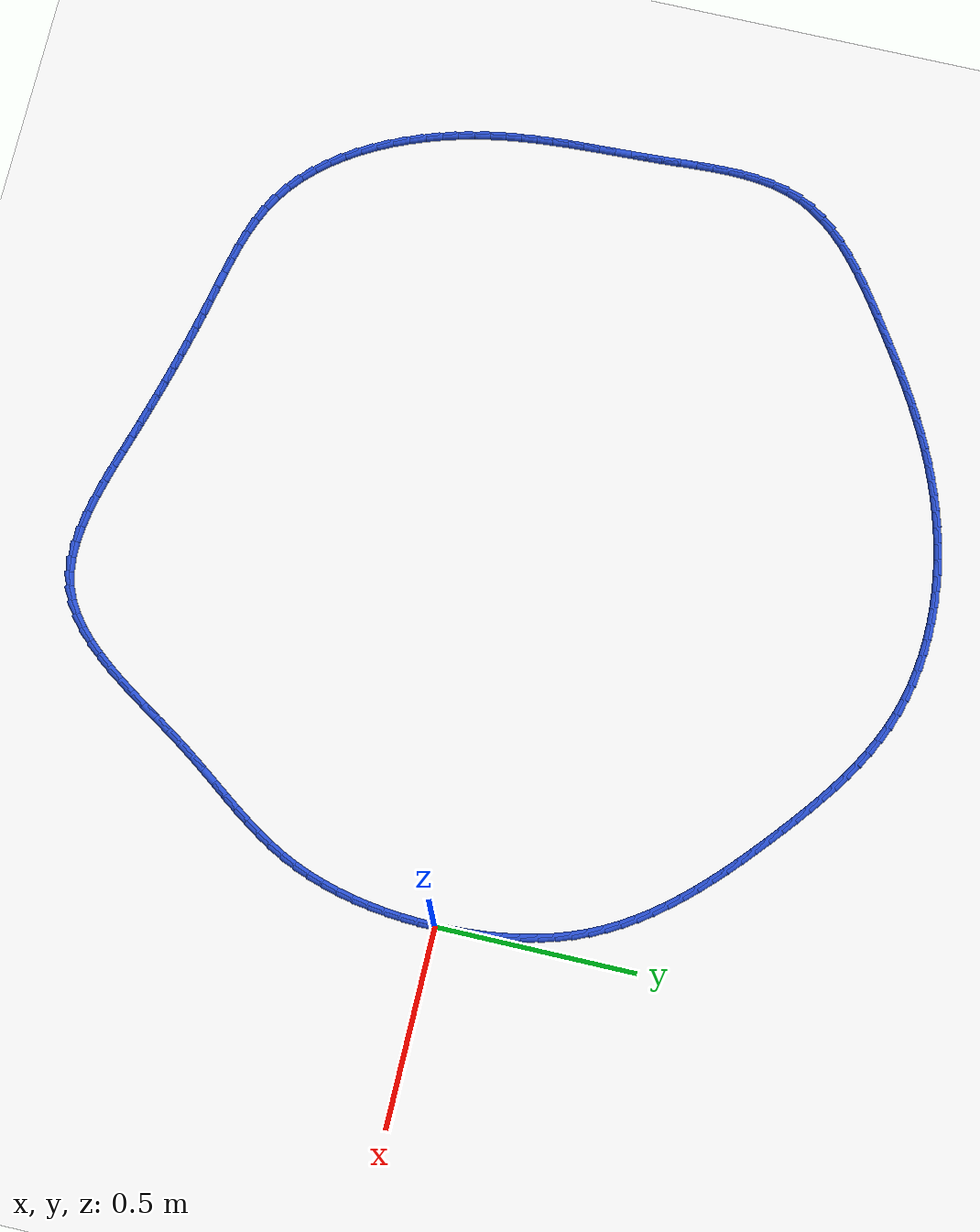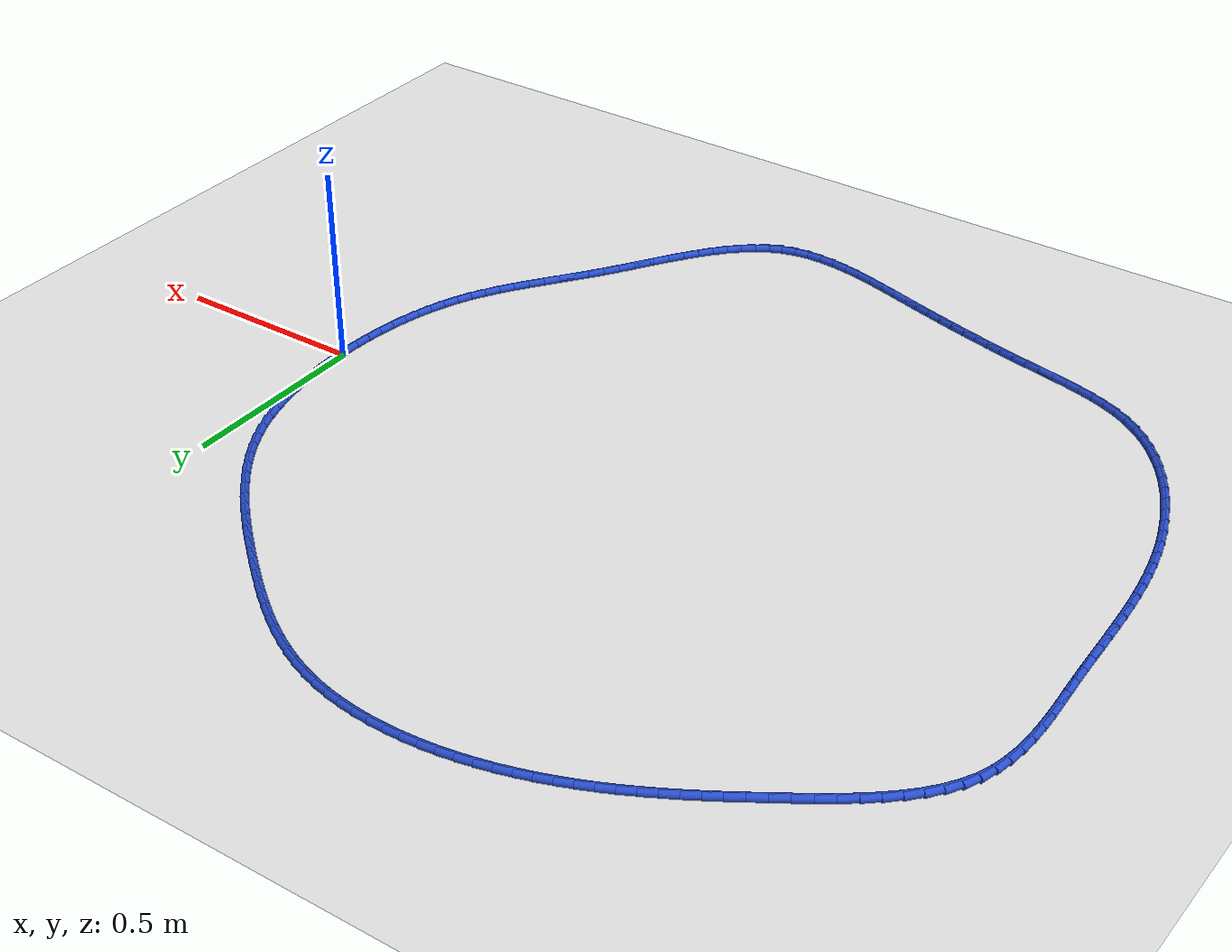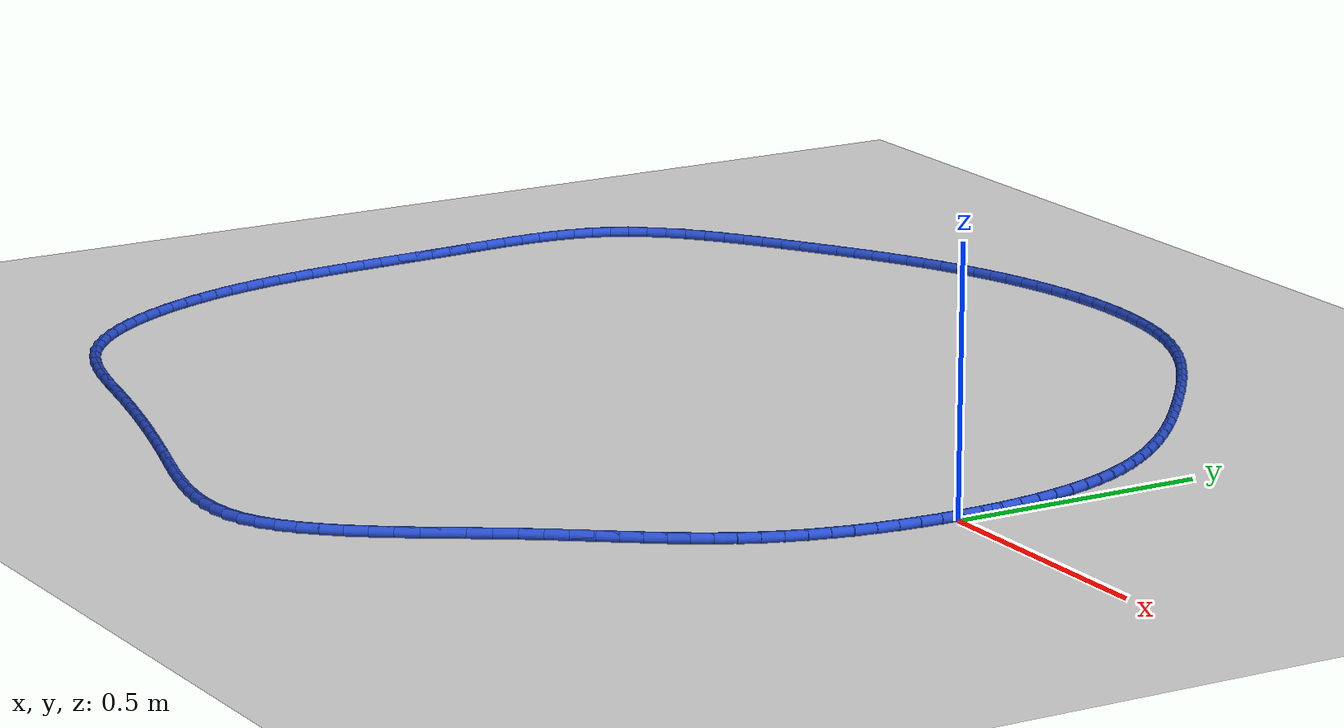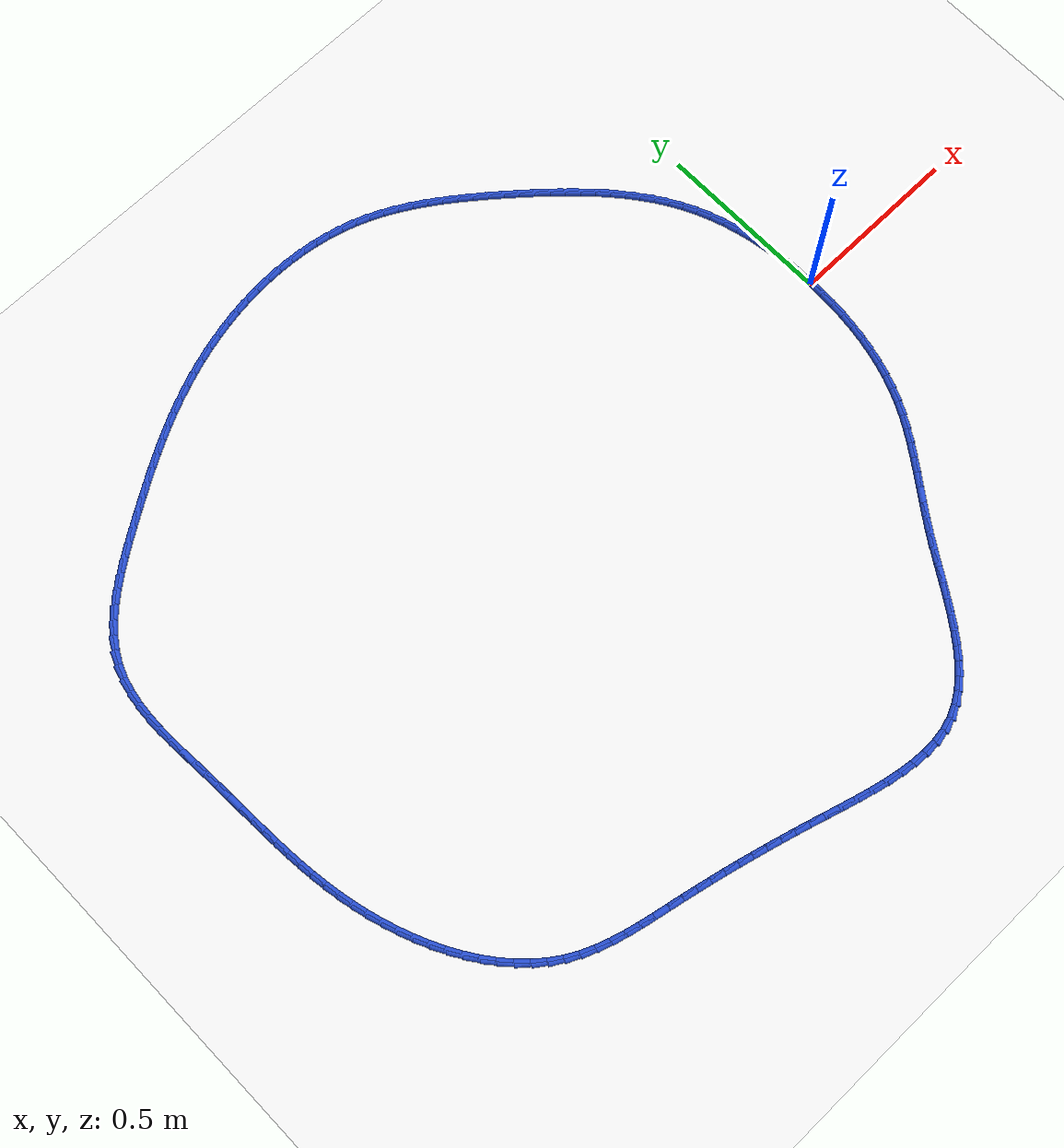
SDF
<sdf version="1.6">
 <world name="default">
  <light name="sun" type="directional">
   <pose>0 0 10 0 -0 0</pose>
   <diffuse>0.8 0.8 0.8 1</diffuse>
   <specular>0.2 0.2 0.2 1</specular>
   <attenuation>
    <range>1000</range>
    <constant>0.9</constant>
    <linear>0.01</linear>
    <quadratic>0.001</quadratic>
   </attenuation>
   <direction>-0.5 0.1 -0.9</direction>
  </light>
  <model name="ground_plane">
   <static>1</static>
   <link name="link">
    <collision name="collision">
     <geometry><plane><normal>0 0 1</normal><size>100 100</size></plane></geometry>
     <surface><friction><ode><mu>100</mu><mu2>50</mu2></ode></friction></surface>
    </collision>
    <visual name="visual">
     <cast_shadows>0</cast_shadows>
     <geometry><plane><normal>0 0 1</normal><size>100 100</size></plane></geometry>
     <material>
      <script><uri>file://media/materials/scripts/gazebo.material</uri><name>Gazebo/WhiteGlow</name></script>
     </material>
    </visual>
   </link>
  </model>
  <gravity>0 0 -9.8</gravity>
  <magnetic_field>6e-06 2.3e-05 -4.2e-05</magnetic_field>
  <atmosphere type="adiabatic"/>
  <physics name="default_physics" default="0" type="ode">
   <max_step_size>0.001</max_step_size>
   <real_time_factor>1</real_time_factor>
   <real_time_update_rate>1000</real_time_update_rate>
  </physics>
  <scene><ambient>0.4 0.4 0.4 1</ambient><background>0.7 0.7 0.7 1</background><shadows>1</shadows></scene>
  <spherical_coordinates>
   <surface_model>EARTH_WGS84</surface_model>
   <latitude_deg>0</latitude_deg>
   <longitude_deg>0</longitude_deg>
   <elevation>0</elevation>
   <heading_deg>0</heading_deg>
  </spherical_coordinates>
  <model name="line">
   <link name="link_0">
    <pose>-9.540979117872439e-18 -1.8041124150158794e-16 0.01 0 1.57 -1.5562641563522297</pose>
    <collision name="collision">
     <geometry><cylinder><radius>0.01</radius><length>0.08</length></cylinder></geometry>
    </collision>
    <visual name="visual">
     <material>
      <script><name>Gazebo/Blue</name><uri>file://media/materials/scripts/gazebo.material</uri></script>
     </material>
     <geometry><cylinder><radius>0.01</radius><length>0.08</length></cylinder></geometry>
    </visual>
   </link>
   <link name="link_1">
    <pose>-0.0006135620323382339 0.04221797718795061 0.01 0 1.57 -1.5198698199850857</pose>
    <collision name="collision">
     <geometry><cylinder><radius>0.01</radius><length>0.08</length></cylinder></geometry>
    </collision>
    <visual name="visual">
     <material>
      <script><name>Gazebo/Blue</name><uri>file://media/materials/scripts/gazebo.material</uri></script>
     </material>
     <geometry><cylinder><radius>0.01</radius><length>0.08</length></cylinder></geometry>
    </visual>
   </link>
   <link name="link_2">
    <pose>-0.002757716761446359 0.08428449449831325 0.01 0 1.57 -1.481096238251609</pose>
    <collision name="collision">
     <geometry><cylinder><radius>0.01</radius><length>0.08</length></cylinder></geometry>
    </collision>
    <visual name="visual">
     <material>
      <script><name>Gazebo/Blue</name><uri>file://media/materials/scripts/gazebo.material</uri></script>
     </material>
     <geometry><cylinder><radius>0.01</radius><length>0.08</length></cylinder></geometry>
    </visual>
   </link>
   <link name="link_3">
    <pose>-0.006516698007625079 0.1260781445897635 0.01 0 1.57 -1.4397135661033738</pose>
    <collision name="collision">
     <geometry><cylinder><radius>0.01</radius><length>0.08</length></cylinder></geometry>
    </collision>
    <visual name="visual">
     <material>
      <script><name>Gazebo/Blue</name><uri>file://media/materials/scripts/gazebo.material</uri></script>
     </material>
     <geometry><cylinder><radius>0.01</radius><length>0.08</length></cylinder></geometry>
    </visual>
   </link>
   <link name="link_4">
    <pose>-0.011974739591175069 0.16747752012097702 0.01 0 1.57 -1.3954940215166036</pose>
    <collision name="collision">
     <geometry><cylinder><radius>0.01</radius><length>0.08</length></cylinder></geometry>
    </collision>
    <visual name="visual">
     <material>
      <script><name>Gazebo/Blue</name><uri>file://media/materials/scripts/gazebo.material</uri></script>
     </material>
     <geometry><cylinder><radius>0.01</radius><length>0.08</length></cylinder></geometry>
    </visual>
   </link>
   <link name="link_5">
    <pose>-0.019216075332397026 0.20836121375062963 0.01 0 1.57 -1.3482198838029444</pose>
    <collision name="collision">
     <geometry><cylinder><radius>0.01</radius><length>0.08</length></cylinder></geometry>
    </collision>
    <visual name="visual">
     <material>
      <script><name>Gazebo/Blue</name><uri>file://media/materials/scripts/gazebo.material</uri></script>
     </material>
     <geometry><cylinder><radius>0.01</radius><length>0.08</length></cylinder></geometry>
    </visual>
   </link>
   <link name="link_6">
    <pose>-0.028324939051591648 0.24860781813739713 0.01 0 1.57 -1.2976947429981673</pose>
    <collision name="collision">
     <geometry><cylinder><radius>0.01</radius><length>0.08</length></cylinder></geometry>
    </collision>
    <visual name="visual">
     <material>
      <script><name>Gazebo/Blue</name><uri>file://media/materials/scripts/gazebo.material</uri></script>
     </material>
     <geometry><cylinder><radius>0.01</radius><length>0.08</length></cylinder></geometry>
    </visual>
   </link>
   <link name="link_7">
    <pose>-0.039385564569059596 0.28809592593995503 0.01 0 1.57 -1.2437584107724207</pose>
    <collision name="collision">
     <geometry><cylinder><radius>0.01</radius><length>0.08</length></cylinder></geometry>
    </collision>
    <visual name="visual">
     <material>
      <script><name>Gazebo/Blue</name><uri>file://media/materials/scripts/gazebo.material</uri></script>
     </material>
     <geometry><cylinder><radius>0.01</radius><length>0.08</length></cylinder></geometry>
    </visual>
   </link>
   <link name="link_8">
    <pose>-0.05248218570510156 0.32670412981697927 0.01 0 1.57 -1.1863055565738456</pose>
    <collision name="collision">
     <geometry><cylinder><radius>0.01</radius><length>0.08</length></cylinder></geometry>
    </collision>
    <visual name="visual">
     <material>
      <script><name>Gazebo/Blue</name><uri>file://media/materials/scripts/gazebo.material</uri></script>
     </material>
     <geometry><cylinder><radius>0.01</radius><length>0.08</length></cylinder></geometry>
    </visual>
   </link>
   <link name="link_9">
    <pose>-0.06769903628001825 0.36431102242714564 0.01 0 1.57 -1.1254668795794538</pose>
    <collision name="collision">
     <geometry><cylinder><radius>0.01</radius><length>0.08</length></cylinder></geometry>
    </collision>
    <visual name="visual">
     <material>
      <script><name>Gazebo/Blue</name><uri>file://media/materials/scripts/gazebo.material</uri></script>
     </material>
     <geometry><cylinder><radius>0.01</radius><length>0.08</length></cylinder></geometry>
    </visual>
   </link>
   <link name="link_10">
    <pose>-0.08511510190029276 0.4007991604373144 0.01 0 1.57 -1.065020215708269</pose>
    <collision name="collision">
     <geometry><cylinder><radius>0.01</radius><length>0.08</length></cylinder></geometry>
    </collision>
    <visual name="visual">
     <material>
      <script><name>Gazebo/Blue</name><uri>file://media/materials/scripts/gazebo.material</uri></script>
     </material>
     <geometry><cylinder><radius>0.01</radius><length>0.08</length></cylinder></geometry>
    </visual>
   </link>
   <link name="link_11">
    <pose>-0.10468893227898371 0.4361420664855971 0.01 0 1.57 -1.0089278615824955</pose>
    <collision name="collision">
     <geometry><cylinder><radius>0.01</radius><length>0.08</length></cylinder></geometry>
    </collision>
    <visual name="visual">
     <material>
      <script><name>Gazebo/Blue</name><uri>file://media/materials/scripts/gazebo.material</uri></script>
     </material>
     <geometry><cylinder><radius>0.01</radius><length>0.08</length></cylinder></geometry>
    </visual>
   </link>
   <link name="link_12">
    <pose>-0.12625879272094415 0.4704041147636393 0.01 0 1.57 -0.957566097725728</pose>
    <collision name="collision">
     <geometry><cylinder><radius>0.01</radius><length>0.08</length></cylinder></geometry>
    </collision>
    <visual name="visual">
     <material>
      <script><name>Gazebo/Blue</name><uri>file://media/materials/scripts/gazebo.material</uri></script>
     </material>
     <geometry><cylinder><radius>0.01</radius><length>0.08</length></cylinder></geometry>
    </visual>
   </link>
   <link name="link_13">
    <pose>-0.1496577306142683 0.5036536205877158 0.01 0 1.57 -0.9110131696677166</pose>
    <collision name="collision">
     <geometry><cylinder><radius>0.01</radius><length>0.08</length></cylinder></geometry>
    </collision>
    <visual name="visual">
     <material>
      <script><name>Gazebo/Blue</name><uri>file://media/materials/scripts/gazebo.material</uri></script>
     </material>
     <geometry><cylinder><radius>0.01</radius><length>0.08</length></cylinder></geometry>
    </visual>
   </link>
   <link name="link_14">
    <pose>-0.17471879334705054 0.5359588992741019 0.01 0 1.57 -0.8692415227313832</pose>
    <collision name="collision">
     <geometry><cylinder><radius>0.01</radius><length>0.08</length></cylinder></geometry>
    </collision>
    <visual name="visual">
     <material>
      <script><name>Gazebo/Blue</name><uri>file://media/materials/scripts/gazebo.material</uri></script>
     </material>
     <geometry><cylinder><radius>0.01</radius><length>0.08</length></cylinder></geometry>
    </visual>
   </link>
   <link name="link_15">
    <pose>-0.201275028307385 0.5673882661390719 0.01 0 1.57 -0.8321508137089795</pose>
    <collision name="collision">
     <geometry><cylinder><radius>0.01</radius><length>0.08</length></cylinder></geometry>
    </collision>
    <visual name="visual">
     <material>
      <script><name>Gazebo/Blue</name><uri>file://media/materials/scripts/gazebo.material</uri></script>
     </material>
     <geometry><cylinder><radius>0.01</radius><length>0.08</length></cylinder></geometry>
    </visual>
   </link>
   <link name="link_16">
    <pose>-0.22915948288336613 0.5980100364989016 0.01 0 1.57 -0.7995969884965745</pose>
    <collision name="collision">
     <geometry><cylinder><radius>0.01</radius><length>0.08</length></cylinder></geometry>
    </collision>
    <visual name="visual">
     <material>
      <script><name>Gazebo/Blue</name><uri>file://media/materials/scripts/gazebo.material</uri></script>
     </material>
     <geometry><cylinder><radius>0.01</radius><length>0.08</length></cylinder></geometry>
    </visual>
   </link>
   <link name="link_17">
    <pose>-0.25820520446308803 0.6278925256698653 0.01 0 1.57 -0.7714161063536621</pose>
    <collision name="collision">
     <geometry><cylinder><radius>0.01</radius><length>0.08</length></cylinder></geometry>
    </collision>
    <visual name="visual">
     <material>
      <script><name>Gazebo/Blue</name><uri>file://media/materials/scripts/gazebo.material</uri></script>
     </material>
     <geometry><cylinder><radius>0.01</radius><length>0.08</length></cylinder></geometry>
    </visual>
   </link>
   <link name="link_18">
    <pose>-0.2882452404346452 0.6571040489682388 0.01 0 1.57 -0.7474428521689799</pose>
    <collision name="collision">
     <geometry><cylinder><radius>0.01</radius><length>0.08</length></cylinder></geometry>
    </collision>
    <visual name="visual">
     <material>
      <script><name>Gazebo/Blue</name><uri>file://media/materials/scripts/gazebo.material</uri></script>
     </material>
     <geometry><cylinder><radius>0.01</radius><length>0.08</length></cylinder></geometry>
    </visual>
   </link>
   <link name="link_19">
    <pose>-0.3191126381861316 0.6857129217102961 0.01 0 1.57 -0.7275243807682512</pose>
    <collision name="collision">
     <geometry><cylinder><radius>0.01</radius><length>0.08</length></cylinder></geometry>
    </collision>
    <visual name="visual">
     <material>
      <script><name>Gazebo/Blue</name><uri>file://media/materials/scripts/gazebo.material</uri></script>
     </material>
     <geometry><cylinder><radius>0.01</radius><length>0.08</length></cylinder></geometry>
    </visual>
   </link>
   <link name="link_20">
    <pose>-0.35064044510564174 0.7137874592123127 0.01 0 1.57 -0.7115304259429328</pose>
    <collision name="collision">
     <geometry><cylinder><radius>0.01</radius><length>0.08</length></cylinder></geometry>
    </collision>
    <visual name="visual">
     <material>
      <script><name>Gazebo/Blue</name><uri>file://media/materials/scripts/gazebo.material</uri></script>
     </material>
     <geometry><cylinder><radius>0.01</radius><length>0.08</length></cylinder></geometry>
    </visual>
   </link>
   <link name="link_21">
    <pose>-0.3826617085812698 0.7413959767905637 0.01 0 1.57 -0.6993419708070425</pose>
    <collision name="collision">
     <geometry><cylinder><radius>0.01</radius><length>0.08</length></cylinder></geometry>
    </collision>
    <visual name="visual">
     <material>
      <script><name>Gazebo/Blue</name><uri>file://media/materials/scripts/gazebo.material</uri></script>
     </material>
     <geometry><cylinder><radius>0.01</radius><length>0.08</length></cylinder></geometry>
    </visual>
   </link>
   <link name="link_22">
    <pose>-0.4150100092556313 0.7686062071653443 0.01 0 1.57 -0.688283045462947</pose>
    <collision name="collision">
     <geometry><cylinder><radius>0.01</radius><length>0.08</length></cylinder></geometry>
    </collision>
    <visual name="visual">
     <material>
      <script><name>Gazebo/Blue</name><uri>file://media/materials/scripts/gazebo.material</uri></script>
     </material>
     <geometry><cylinder><radius>0.01</radius><length>0.08</length></cylinder></geometry>
    </visual>
   </link>
   <link name="link_23">
    <pose>-0.4475933912645606 0.7954045295380407 0.01 0 1.57 -0.673016336437079</pose>
    <collision name="collision">
     <geometry><cylinder><radius>0.01</radius><length>0.08</length></cylinder></geometry>
    </collision>
    <visual name="visual">
     <material>
      <script><name>Gazebo/Blue</name><uri>file://media/materials/scripts/gazebo.material</uri></script>
     </material>
     <geometry><cylinder><radius>0.01</radius><length>0.08</length></cylinder></geometry>
    </visual>
   </link>
   <link name="link_24">
    <pose>-0.4804701985864686 0.821613116187204 0.01 0 1.57 -0.6527961505215211</pose>
    <collision name="collision">
     <geometry><cylinder><radius>0.01</radius><length>0.08</length></cylinder></geometry>
    </collision>
    <visual name="visual">
     <material>
      <script><name>Gazebo/Blue</name><uri>file://media/materials/scripts/gazebo.material</uri></script>
     </material>
     <geometry><cylinder><radius>0.01</radius><length>0.08</length></cylinder></geometry>
    </visual>
   </link>
   <link name="link_25">
    <pose>-0.5137168638381131 0.8470343770310894 0.01 0 1.57 -0.6274823242342976</pose>
    <collision name="collision">
     <geometry><cylinder><radius>0.01</radius><length>0.08</length></cylinder></geometry>
    </collision>
    <visual name="visual">
     <material>
      <script><name>Gazebo/Blue</name><uri>file://media/materials/scripts/gazebo.material</uri></script>
     </material>
     <geometry><cylinder><radius>0.01</radius><length>0.08</length></cylinder></geometry>
    </visual>
   </link>
   <link name="link_26">
    <pose>-0.5474098196362523 0.8714707219879527 0.01 0 1.57 -0.5969203490022805</pose>
    <collision name="collision">
     <geometry><cylinder><radius>0.01</radius><length>0.08</length></cylinder></geometry>
    </collision>
    <visual name="visual">
     <material>
      <script><name>Gazebo/Blue</name><uri>file://media/materials/scripts/gazebo.material</uri></script>
     </material>
     <geometry><cylinder><radius>0.01</radius><length>0.08</length></cylinder></geometry>
    </visual>
   </link>
   <link name="link_27">
    <pose>-0.5816254985976443 0.8947245609760495 0.01 0 1.57 -0.560960227581564</pose>
    <collision name="collision">
     <geometry><cylinder><radius>0.01</radius><length>0.08</length></cylinder></geometry>
    </collision>
    <visual name="visual">
     <material>
      <script><name>Gazebo/Blue</name><uri>file://media/materials/scripts/gazebo.material</uri></script>
     </material>
     <geometry><cylinder><radius>0.01</radius><length>0.08</length></cylinder></geometry>
    </visual>
   </link>
   <link name="link_28">
    <pose>-0.6164403333390471 0.9165983039136354 0.01 0 1.57 -0.5194819737954144</pose>
    <collision name="collision">
     <geometry><cylinder><radius>0.01</radius><length>0.08</length></cylinder></geometry>
    </collision>
    <visual name="visual">
     <material>
      <script><name>Gazebo/Blue</name><uri>file://media/materials/scripts/gazebo.material</uri></script>
     </material>
     <geometry><cylinder><radius>0.01</radius><length>0.08</length></cylinder></geometry>
    </visual>
   </link>
   <link name="link_29">
    <pose>-0.6519307564772188 0.9368943607189664 0.01 0 1.57 -0.47242834214540913</pose>
    <collision name="collision">
     <geometry><cylinder><radius>0.01</radius><length>0.08</length></cylinder></geometry>
    </collision>
    <visual name="visual">
     <material>
      <script><name>Gazebo/Blue</name><uri>file://media/materials/scripts/gazebo.material</uri></script>
     </material>
     <geometry><cylinder><radius>0.01</radius><length>0.08</length></cylinder></geometry>
    </visual>
   </link>
   <link name="link_30">
    <pose>-0.6881732006289171 0.9554151413102973 0.01 0 1.57 -0.4198441114655215</pose>
    <collision name="collision">
     <geometry><cylinder><radius>0.01</radius><length>0.08</length></cylinder></geometry>
    </collision>
    <visual name="visual">
     <material>
      <script><name>Gazebo/Blue</name><uri>file://media/materials/scripts/gazebo.material</uri></script>
     </material>
     <geometry><cylinder><radius>0.01</radius><length>0.08</length></cylinder></geometry>
    </visual>
   </link>
   <link name="link_31">
    <pose>-0.7252440984109008 0.9719630556058846 0.01 0 1.57 -0.36191908760934804</pose>
    <collision name="collision">
     <geometry><cylinder><radius>0.01</radius><length>0.08</length></cylinder></geometry>
    </collision>
    <visual name="visual">
     <material>
      <script><name>Gazebo/Blue</name><uri>file://media/materials/scripts/gazebo.material</uri></script>
     </material>
     <geometry><cylinder><radius>0.01</radius><length>0.08</length></cylinder></geometry>
    </visual>
   </link>
   <link name="link_32">
    <pose>-0.763219882439927 0.9863405135239829 0.01 0 1.57 -0.300039057551947</pose>
    <collision name="collision">
     <geometry><cylinder><radius>0.01</radius><length>0.08</length></cylinder></geometry>
    </collision>
    <visual name="visual">
     <material>
      <script><name>Gazebo/Blue</name><uri>file://media/materials/scripts/gazebo.material</uri></script>
     </material>
     <geometry><cylinder><radius>0.01</radius><length>0.08</length></cylinder></geometry>
    </visual>
   </link>
   <link name="link_33">
    <pose>-0.8021480729315696 0.9983840799239451 0.01 0 1.57 -0.23974730684993473</pose>
    <collision name="collision">
     <geometry><cylinder><radius>0.01</radius><length>0.08</length></cylinder></geometry>
    </collision>
    <visual name="visual">
     <material>
      <script><name>Gazebo/Blue</name><uri>file://media/materials/scripts/gazebo.material</uri></script>
     </material>
     <geometry><cylinder><radius>0.01</radius><length>0.08</length></cylinder></geometry>
    </visual>
   </link>
   <link name="link_34">
    <pose>-0.8419259949555972 1.0081077489393275 0.01 0 1.57 -0.18262299285056854</pose>
    <collision name="collision">
     <geometry><cylinder><radius>0.01</radius><length>0.08</length></cylinder></geometry>
    </collision>
    <visual name="visual">
     <material>
      <script><name>Gazebo/Blue</name><uri>file://media/materials/scripts/gazebo.material</uri></script>
     </material>
     <geometry><cylinder><radius>0.01</radius><length>0.08</length></cylinder></geometry>
    </visual>
   </link>
   <link name="link_35">
    <pose>-0.8824023539237134 1.015582950319179 0.01 0 1.57 -0.12843929787147793</pose>
    <collision name="collision">
     <geometry><cylinder><radius>0.01</radius><length>0.08</length></cylinder></geometry>
    </collision>
    <visual name="visual">
     <material>
      <script><name>Gazebo/Blue</name><uri>file://media/materials/scripts/gazebo.material</uri></script>
     </material>
     <geometry><cylinder><radius>0.01</radius><length>0.08</length></cylinder></geometry>
    </visual>
   </link>
   <link name="link_36">
    <pose>-0.923425830469115 1.0208811430840141 0.01 0 1.57 -0.07692898076230842</pose>
    <collision name="collision">
     <geometry><cylinder><radius>0.01</radius><length>0.08</length></cylinder></geometry>
    </collision>
    <visual name="visual">
     <material>
      <script><name>Gazebo/Blue</name><uri>file://media/materials/scripts/gazebo.material</uri></script>
     </material>
     <geometry><cylinder><radius>0.01</radius><length>0.08</length></cylinder></geometry>
    </visual>
   </link>
   <link name="link_37">
    <pose>-0.9648451052249976 1.0240737862543494 0.01 0 1.57 -0.02780004251649934</pose>
    <collision name="collision">
     <geometry><cylinder><radius>0.01</radius><length>0.08</length></cylinder></geometry>
    </collision>
    <visual name="visual">
     <material>
      <script><name>Gazebo/Blue</name><uri>file://media/materials/scripts/gazebo.material</uri></script>
     </material>
     <geometry><cylinder><radius>0.01</radius><length>0.08</length></cylinder></geometry>
    </visual>
   </link>
   <link name="link_38">
    <pose>-1.0065088588245583 1.0252323388507019 0.01 0 1.57 0.01925380818703091</pose>
    <collision name="collision">
     <geometry><cylinder><radius>0.01</radius><length>0.08</length></cylinder></geometry>
    </collision>
    <visual name="visual">
     <material>
      <script><name>Gazebo/Blue</name><uri>file://media/materials/scripts/gazebo.material</uri></script>
     </material>
     <geometry><cylinder><radius>0.01</radius><length>0.08</length></cylinder></geometry>
    </visual>
   </link>
   <link name="link_39">
    <pose>-1.0482657719009927 1.0244282598935865 0.01 0 1.57 0.06454647241102049</pose>
    <collision name="collision">
     <geometry><cylinder><radius>0.01</radius><length>0.08</length></cylinder></geometry>
    </collision>
    <visual name="visual">
     <material>
      <script><name>Gazebo/Blue</name><uri>file://media/materials/scripts/gazebo.material</uri></script>
     </material>
     <geometry><cylinder><radius>0.01</radius><length>0.08</length></cylinder></geometry>
    </visual>
   </link>
   <link name="link_40">
    <pose>-1.089964525087497 1.0217330084035199 0.01 0 1.57 0.1083959198402164</pose>
    <collision name="collision">
     <geometry><cylinder><radius>0.01</radius><length>0.08</length></cylinder></geometry>
    </collision>
    <visual name="visual">
     <material>
      <script><name>Gazebo/Blue</name><uri>file://media/materials/scripts/gazebo.material</uri></script>
     </material>
     <geometry><cylinder><radius>0.01</radius><length>0.08</length></cylinder></geometry>
    </visual>
   </link>
   <link name="link_41">
    <pose>-1.1314537990172686 1.0172180434010187 0.01 0 1.57 0.15100625188747505</pose>
    <collision name="collision">
     <geometry><cylinder><radius>0.01</radius><length>0.08</length></cylinder></geometry>
    </collision>
    <visual name="visual">
     <material>
      <script><name>Gazebo/Blue</name><uri>file://media/materials/scripts/gazebo.material</uri></script>
     </material>
     <geometry><cylinder><radius>0.01</radius><length>0.08</length></cylinder></geometry>
    </visual>
   </link>
   <link name="link_42">
    <pose>-1.1725995096842836 1.0109571223223863 0.01 0 1.57 0.19209577911662537</pose>
    <collision name="collision">
     <geometry><cylinder><radius>0.01</radius><length>0.08</length></cylinder></geometry>
    </collision>
    <visual name="visual">
     <material>
      <script><name>Gazebo/Blue</name><uri>file://media/materials/scripts/gazebo.material</uri></script>
     </material>
     <geometry><cylinder><radius>0.01</radius><length>0.08</length></cylinder></geometry>
    </visual>
   </link>
   <link name="link_43">
    <pose>-1.2133390233742982 1.003033530833753 0.01 0 1.57 0.23157736933684694</pose>
    <collision name="collision">
     <geometry><cylinder><radius>0.01</radius><length>0.08</length></cylinder></geometry>
    </collision>
    <visual name="visual">
     <material>
      <script><name>Gazebo/Blue</name><uri>file://media/materials/scripts/gazebo.material</uri></script>
     </material>
     <geometry><cylinder><radius>0.01</radius><length>0.08</length></cylinder></geometry>
    </visual>
   </link>
   <link name="link_44">
    <pose>-1.2536282188155174 0.9935330233218368 0.01 0 1.57 0.2694898467344561</pose>
    <collision name="collision">
     <geometry><cylinder><radius>0.01</radius><length>0.08</length></cylinder></geometry>
    </collision>
    <visual name="visual">
     <material>
      <script><name>Gazebo/Blue</name><uri>file://media/materials/scripts/gazebo.material</uri></script>
     </material>
     <geometry><cylinder><radius>0.01</radius><length>0.08</length></cylinder></geometry>
    </visual>
   </link>
   <link name="link_45">
    <pose>-1.2934229747663595 0.9825413541773845 0.01 0 1.57 0.30588774677672725</pose>
    <collision name="collision">
     <geometry><cylinder><radius>0.01</radius><length>0.08</length></cylinder></geometry>
    </collision>
    <visual name="visual">
     <material>
      <script><name>Gazebo/Blue</name><uri>file://media/materials/scripts/gazebo.material</uri></script>
     </material>
     <geometry><cylinder><radius>0.01</radius><length>0.08</length></cylinder></geometry>
    </visual>
   </link>
   <link name="link_46">
    <pose>-1.332679169985244 0.9701442777911438 0.01 0 1.57 0.3408381588892178</pose>
    <collision name="collision">
     <geometry><cylinder><radius>0.01</radius><length>0.08</length></cylinder></geometry>
    </collision>
    <visual name="visual">
     <material>
      <script><name>Gazebo/Blue</name><uri>file://media/materials/scripts/gazebo.material</uri></script>
     </material>
     <geometry><cylinder><radius>0.01</radius><length>0.08</length></cylinder></geometry>
    </visual>
   </link>
   <link name="link_47">
    <pose>-1.3713526832305882 0.9564275485538609 0.01 0 1.57 0.3744179940940921</pose>
    <collision name="collision">
     <geometry><cylinder><radius>0.01</radius><length>0.08</length></cylinder></geometry>
    </collision>
    <visual name="visual">
     <material>
      <script><name>Gazebo/Blue</name><uri>file://media/materials/scripts/gazebo.material</uri></script>
     </material>
     <geometry><cylinder><radius>0.01</radius><length>0.08</length></cylinder></geometry>
    </visual>
   </link>
   <link name="link_48">
    <pose>-1.4093993932608124 0.9414769208562834 0.01 0 1.57 0.4067102133469927</pose>
    <collision name="collision">
     <geometry><cylinder><radius>0.01</radius><length>0.08</length></cylinder></geometry>
    </collision>
    <visual name="visual">
     <material>
      <script><name>Gazebo/Blue</name><uri>file://media/materials/scripts/gazebo.material</uri></script>
     </material>
     <geometry><cylinder><radius>0.01</radius><length>0.08</length></cylinder></geometry>
    </visual>
   </link>
   <link name="link_49">
    <pose>-1.4467754011663498 0.9253781199086518 0.01 0 1.57 0.43744680700313454</pose>
    <collision name="collision">
     <geometry><cylinder><radius>0.01</radius><length>0.08</length></cylinder></geometry>
    </collision>
    <visual name="visual">
     <material>
      <script><name>Gazebo/Blue</name><uri>file://media/materials/scripts/gazebo.material</uri></script>
     </material>
     <geometry><cylinder><radius>0.01</radius><length>0.08</length></cylinder></geometry>
    </visual>
   </link>
   <link name="link_50">
    <pose>-1.4834843231324741 0.9082106346870561 0.01 0 1.57 0.46574308001793474</pose>
    <collision name="collision">
     <geometry><cylinder><radius>0.01</radius><length>0.08</length></cylinder></geometry>
    </collision>
    <visual name="visual">
     <material>
      <script><name>Gazebo/Blue</name><uri>file://media/materials/scripts/gazebo.material</uri></script>
     </material>
     <geometry><cylinder><radius>0.01</radius><length>0.08</length></cylinder></geometry>
    </visual>
   </link>
   <link name="link_51">
    <pose>-1.5196359753708333 0.8900400156869055 0.01 0 1.57 0.491267990132445</pose>
    <collision name="collision">
     <geometry><cylinder><radius>0.01</radius><length>0.08</length></cylinder></geometry>
    </collision>
    <visual name="visual">
     <material>
      <script><name>Gazebo/Blue</name><uri>file://media/materials/scripts/gazebo.material</uri></script>
     </material>
     <geometry><cylinder><radius>0.01</radius><length>0.08</length></cylinder></geometry>
    </visual>
   </link>
   <link name="link_52">
    <pose>-1.5553545727682416 0.8709299236144786 0.01 0 1.57 0.5138452623770677</pose>
    <collision name="collision">
     <geometry><cylinder><radius>0.01</radius><length>0.08</length></cylinder></geometry>
    </collision>
    <visual name="visual">
     <material>
      <script><name>Gazebo/Blue</name><uri>file://media/materials/scripts/gazebo.material</uri></script>
     </material>
     <geometry><cylinder><radius>0.01</radius><length>0.08</length></cylinder></geometry>
    </visual>
   </link>
   <link name="link_53">
    <pose>-1.5907643302115149 0.8509440191760532 0.01 0 1.57 0.5333547266603141</pose>
    <collision name="collision">
     <geometry><cylinder><radius>0.01</radius><length>0.08</length></cylinder></geometry>
    </collision>
    <visual name="visual">
     <material>
      <script><name>Gazebo/Blue</name><uri>file://media/materials/scripts/gazebo.material</uri></script>
     </material>
     <geometry><cylinder><radius>0.01</radius><length>0.08</length></cylinder></geometry>
    </visual>
   </link>
   <link name="link_54">
    <pose>-1.6259894625874676 0.8301459630779084 0.01 0 1.57 0.5497286316519538</pose>
    <collision name="collision">
     <geometry><cylinder><radius>0.01</radius><length>0.08</length></cylinder></geometry>
    </collision>
    <visual name="visual">
     <material>
      <script><name>Gazebo/Blue</name><uri>file://media/materials/scripts/gazebo.material</uri></script>
     </material>
     <geometry><cylinder><radius>0.01</radius><length>0.08</length></cylinder></geometry>
    </visual>
   </link>
   <link name="link_55">
    <pose>-1.6611541847829139 0.8085994160263218 0.01 0 1.57 0.562946485534427</pose>
    <collision name="collision">
     <geometry><cylinder><radius>0.01</radius><length>0.08</length></cylinder></geometry>
    </collision>
    <visual name="visual">
     <material>
      <script><name>Gazebo/Blue</name><uri>file://media/materials/scripts/gazebo.material</uri></script>
     </material>
     <geometry><cylinder><radius>0.01</radius><length>0.08</length></cylinder></geometry>
    </visual>
   </link>
   <link name="link_56">
    <pose>-1.6963827116846693 0.7863680387275712 0.01 0 1.57 0.5730291810932302</pose>
    <collision name="collision">
     <geometry><cylinder><radius>0.01</radius><length>0.08</length></cylinder></geometry>
    </collision>
    <visual name="visual">
     <material>
      <script><name>Gazebo/Blue</name><uri>file://media/materials/scripts/gazebo.material</uri></script>
     </material>
     <geometry><cylinder><radius>0.01</radius><length>0.08</length></cylinder></geometry>
    </visual>
   </link>
   <link name="link_57">
    <pose>-1.7317992581795485 0.763515491887936 0.01 0 1.57 0.5801263401854877</pose>
    <collision name="collision">
     <geometry><cylinder><radius>0.01</radius><length>0.08</length></cylinder></geometry>
    </collision>
    <visual name="visual">
     <material>
      <script><name>Gazebo/Blue</name><uri>file://media/materials/scripts/gazebo.material</uri></script>
     </material>
     <geometry><cylinder><radius>0.01</radius><length>0.08</length></cylinder></geometry>
    </visual>
   </link>
   <link name="link_58">
    <pose>-1.7675232730939137 0.7401037931918861 0.01 0 1.57 0.5891944055719505</pose>
    <collision name="collision">
     <geometry><cylinder><radius>0.01</radius><length>0.08</length></cylinder></geometry>
    </collision>
    <visual name="visual">
     <material>
      <script><name>Gazebo/Blue</name><uri>file://media/materials/scripts/gazebo.material</uri></script>
     </material>
     <geometry><cylinder><radius>0.01</radius><length>0.08</length></cylinder></geometry>
    </visual>
   </link>
   <link name="link_59">
    <pose>-1.8034234246912977 0.7161085078045296 0.01 0 1.57 0.6074756814900042</pose>
    <collision name="collision">
     <geometry><cylinder><radius>0.01</radius><length>0.08</length></cylinder></geometry>
    </collision>
    <visual name="visual">
     <material>
      <script><name>Gazebo/Blue</name><uri>file://media/materials/scripts/gazebo.material</uri></script>
     </material>
     <geometry><cylinder><radius>0.01</radius><length>0.08</length></cylinder></geometry>
    </visual>
   </link>
   <link name="link_60">
    <pose>-1.8389986553415543 0.6913777439037898 0.01 0 1.57 0.6358760869394062</pose>
    <collision name="collision">
     <geometry><cylinder><radius>0.01</radius><length>0.08</length></cylinder></geometry>
    </collision>
    <visual name="visual">
     <material>
      <script><name>Gazebo/Blue</name><uri>file://media/materials/scripts/gazebo.material</uri></script>
     </material>
     <geometry><cylinder><radius>0.01</radius><length>0.08</length></cylinder></geometry>
    </visual>
   </link>
   <link name="link_61">
    <pose>-1.8737182228083555 0.665749376382515 0.01 0 1.57 0.6751353309402686</pose>
    <collision name="collision">
     <geometry><cylinder><radius>0.01</radius><length>0.08</length></cylinder></geometry>
    </collision>
    <visual name="visual">
     <material>
      <script><name>Gazebo/Blue</name><uri>file://media/materials/scripts/gazebo.material</uri></script>
     </material>
     <geometry><cylinder><radius>0.01</radius><length>0.08</length></cylinder></geometry>
    </visual>
   </link>
   <link name="link_62">
    <pose>-1.9070513848553732 0.6390612801335539 0.01 0 1.57 0.7263685108960141</pose>
    <collision name="collision">
     <geometry><cylinder><radius>0.01</radius><length>0.08</length></cylinder></geometry>
    </collision>
    <visual name="visual">
     <material>
      <script><name>Gazebo/Blue</name><uri>file://media/materials/scripts/gazebo.material</uri></script>
     </material>
     <geometry><cylinder><radius>0.01</radius><length>0.08</length></cylinder></geometry>
    </visual>
   </link>
   <link name="link_63">
    <pose>-1.9384673992462802 0.611151330049755 0.01 0 1.57 0.7909901587287327</pose>
    <collision name="collision">
     <geometry><cylinder><radius>0.01</radius><length>0.08</length></cylinder></geometry>
    </collision>
    <visual name="visual">
     <material>
      <script><name>Gazebo/Blue</name><uri>file://media/materials/scripts/gazebo.material</uri></script>
     </material>
     <geometry><cylinder><radius>0.01</radius><length>0.08</length></cylinder></geometry>
    </visual>
   </link>
   <link name="link_64">
    <pose>-1.9674355237447485 0.581857401023967 0.01 0 1.57 0.8705442751016217</pose>
    <collision name="collision">
     <geometry><cylinder><radius>0.01</radius><length>0.08</length></cylinder></geometry>
    </collision>
    <visual name="visual">
     <material>
      <script><name>Gazebo/Blue</name><uri>file://media/materials/scripts/gazebo.material</uri></script>
     </material>
     <geometry><cylinder><radius>0.01</radius><length>0.08</length></cylinder></geometry>
    </visual>
   </link>
   <link name="link_65">
    <pose>-1.9934250161144502 0.5510173679490381 0.01 0 1.57 0.9663593895171518</pose>
    <collision name="collision">
     <geometry><cylinder><radius>0.01</radius><length>0.08</length></cylinder></geometry>
    </collision>
    <visual name="visual">
     <material>
      <script><name>Gazebo/Blue</name><uri>file://media/materials/scripts/gazebo.material</uri></script>
     </material>
     <geometry><cylinder><radius>0.01</radius><length>0.08</length></cylinder></geometry>
    </visual>
   </link>
   <link name="link_66">
    <pose>-2.0159051341190586 0.518469105717817 0.01 0 1.57 1.078954262658766</pose>
    <collision name="collision">
     <geometry><cylinder><radius>0.01</radius><length>0.08</length></cylinder></geometry>
    </collision>
    <visual name="visual">
     <material>
      <script><name>Gazebo/Blue</name><uri>file://media/materials/scripts/gazebo.material</uri></script>
     </material>
     <geometry><cylinder><radius>0.01</radius><length>0.08</length></cylinder></geometry>
    </visual>
   </link>
   <link name="link_67">
    <pose>-2.034345135522244 0.4840504892231526 0.01 0 1.57 1.2036013778380554</pose>
    <collision name="collision">
     <geometry><cylinder><radius>0.01</radius><length>0.08</length></cylinder></geometry>
    </collision>
    <visual name="visual">
     <material>
      <script><name>Gazebo/Blue</name><uri>file://media/materials/scripts/gazebo.material</uri></script>
     </material>
     <geometry><cylinder><radius>0.01</radius><length>0.08</length></cylinder></geometry>
    </visual>
   </link>
   <link name="link_68">
    <pose>-2.0483453213435636 0.4476522999408986 0.01 0 1.57 1.3174472961279797</pose>
    <collision name="collision">
     <geometry><cylinder><radius>0.01</radius><length>0.08</length></cylinder></geometry>
    </collision>
    <visual name="visual">
     <material>
      <script><name>Gazebo/Blue</name><uri>file://media/materials/scripts/gazebo.material</uri></script>
     </material>
     <geometry><cylinder><radius>0.01</radius><length>0.08</length></cylinder></geometry>
    </visual>
   </link>
   <link name="link_69">
    <pose>-2.058233979195863 0.40945923209247803 0.01 0 1.57 1.412031176600392</pose>
    <collision name="collision">
     <geometry><cylinder><radius>0.01</radius><length>0.08</length></cylinder></geometry>
    </collision>
    <visual name="visual">
     <material>
      <script><name>Gazebo/Blue</name><uri>file://media/materials/scripts/gazebo.material</uri></script>
     </material>
     <geometry><cylinder><radius>0.01</radius><length>0.08</length></cylinder></geometry>
    </visual>
   </link>
   <link name="link_70">
    <pose>-2.0645907380626425 0.3697574548893827 0.01 0 1.57 1.4877915944481888</pose>
    <collision name="collision">
     <geometry><cylinder><radius>0.01</radius><length>0.08</length></cylinder></geometry>
    </collision>
    <visual name="visual">
     <material>
      <script><name>Gazebo/Blue</name><uri>file://media/materials/scripts/gazebo.material</uri></script>
     </material>
     <geometry><cylinder><radius>0.01</radius><length>0.08</length></cylinder></geometry>
    </visual>
   </link>
   <link name="link_71">
    <pose>-2.0679954649666734 0.3288332336475866 0.01 0 1.57 1.5461345313920896</pose>
    <collision name="collision">
     <geometry><cylinder><radius>0.01</radius><length>0.08</length></cylinder></geometry>
    </collision>
    <visual name="visual">
     <material>
      <script><name>Gazebo/Blue</name><uri>file://media/materials/scripts/gazebo.material</uri></script>
     </material>
     <geometry><cylinder><radius>0.01</radius><length>0.08</length></cylinder></geometry>
    </visual>
   </link>
   <link name="link_72">
    <pose>-2.0690280269307246 0.2869728336830651 0.01 0 1.57 -1.5529264260222502</pose>
    <collision name="collision">
     <geometry><cylinder><radius>0.01</radius><length>0.08</length></cylinder></geometry>
    </collision>
    <visual name="visual">
     <material>
      <script><name>Gazebo/Blue</name><uri>file://media/materials/scripts/gazebo.material</uri></script>
     </material>
     <geometry><cylinder><radius>0.01</radius><length>0.08</length></cylinder></geometry>
    </visual>
   </link>
   <link name="link_73">
    <pose>-2.0682682909775676 0.24446252031179166 0.01 0 1.57 -1.5248295544569161</pose>
    <collision name="collision">
     <geometry><cylinder><radius>0.01</radius><length>0.08</length></cylinder></geometry>
    </collision>
    <visual name="visual">
     <material>
      <script><name>Gazebo/Blue</name><uri>file://media/materials/scripts/gazebo.material</uri></script>
     </material>
     <geometry><cylinder><radius>0.01</radius><length>0.08</length></cylinder></geometry>
    </visual>
   </link>
   <link name="link_74">
    <pose>-2.066296124129972 0.20158855884974172 0.01 0 1.57 -1.5102267524517694</pose>
    <collision name="collision">
     <geometry><cylinder><radius>0.01</radius><length>0.08</length></cylinder></geometry>
    </collision>
    <visual name="visual">
     <material>
      <script><name>Gazebo/Blue</name><uri>file://media/materials/scripts/gazebo.material</uri></script>
     </material>
     <geometry><cylinder><radius>0.01</radius><length>0.08</length></cylinder></geometry>
    </visual>
   </link>
   <link name="link_75">
    <pose>-2.063691393410707 0.15863721461288932 0.01 0 1.57 -1.5087032394584863</pose>
    <collision name="collision">
     <geometry><cylinder><radius>0.01</radius><length>0.08</length></cylinder></geometry>
    </collision>
    <visual name="visual">
     <material>
      <script><name>Gazebo/Blue</name><uri>file://media/materials/scripts/gazebo.material</uri></script>
     </material>
     <geometry><cylinder><radius>0.01</radius><length>0.08</length></cylinder></geometry>
    </visual>
   </link>
   <link name="link_76">
    <pose>-2.061033965842544 0.11589475291720863 0.01 0 1.57 -1.5178229557200877</pose>
    <collision name="collision">
     <geometry><cylinder><radius>0.01</radius><length>0.08</length></cylinder></geometry>
    </collision>
    <visual name="visual">
     <material>
      <script><name>Gazebo/Blue</name><uri>file://media/materials/scripts/gazebo.material</uri></script>
     </material>
     <geometry><cylinder><radius>0.01</radius><length>0.08</length></cylinder></geometry>
    </visual>
   </link>
   <link name="link_77">
    <pose>-2.058791208673687 0.07359691775617512 0.01 0 1.57 -1.5260991968962858</pose>
    <collision name="collision">
     <geometry><cylinder><radius>0.01</radius><length>0.08</length></cylinder></geometry>
    </collision>
    <visual name="visual">
     <material>
      <script><name>Gazebo/Blue</name><uri>file://media/materials/scripts/gazebo.material</uri></script>
     </material>
     <geometry><cylinder><radius>0.01</radius><length>0.08</length></cylinder></geometry>
    </visual>
   </link>
   <link name="link_78">
    <pose>-2.056919524479739 0.03174998945446602 0.01 0 1.57 -1.5300708875525295</pose>
    <collision name="collision">
     <geometry><cylinder><radius>0.01</radius><length>0.08</length></cylinder></geometry>
    </collision>
    <visual name="visual">
     <material>
      <script><name>Gazebo/Blue</name><uri>file://media/materials/scripts/gazebo.material</uri></script>
     </material>
     <geometry><cylinder><radius>0.01</radius><length>0.08</length></cylinder></geometry>
    </visual>
   </link>
   <link name="link_79">
    <pose>-2.0552303233472844 -0.009704864791919884 0.01 0 1.57 -1.5295927389093067</pose>
    <collision name="collision">
     <geometry><cylinder><radius>0.01</radius><length>0.08</length></cylinder></geometry>
    </collision>
    <visual name="visual">
     <material>
      <script><name>Gazebo/Blue</name><uri>file://media/materials/scripts/gazebo.material</uri></script>
     </material>
     <geometry><cylinder><radius>0.01</radius><length>0.08</length></cylinder></geometry>
    </visual>
   </link>
   <link name="link_80">
    <pose>-2.0535350056637443 -0.05082648214267887 0.01 0 1.57 -1.5245584961406977</pose>
    <collision name="collision">
     <geometry><cylinder><radius>0.01</radius><length>0.08</length></cylinder></geometry>
    </collision>
    <visual name="visual">
     <material>
      <script><name>Gazebo/Blue</name><uri>file://media/materials/scripts/gazebo.material</uri></script>
     </material>
     <geometry><cylinder><radius>0.01</radius><length>0.08</length></cylinder></geometry>
    </visual>
   </link>
   <link name="link_81">
    <pose>-2.051644971816539 -0.09167369975750679 0.01 0 1.57 -1.5149043902571218</pose>
    <collision name="collision">
     <geometry><cylinder><radius>0.01</radius><length>0.08</length></cylinder></geometry>
    </collision>
    <visual name="visual">
     <material>
      <script><name>Gazebo/Blue</name><uri>file://media/materials/scripts/gazebo.material</uri></script>
     </material>
     <geometry><cylinder><radius>0.01</radius><length>0.08</length></cylinder></geometry>
    </visual>
   </link>
   <link name="link_82">
    <pose>-2.0493716221930893 -0.1323053547961002 0.01 0 1.57 -1.5006148069085803</pose>
    <collision name="collision">
     <geometry><cylinder><radius>0.01</radius><length>0.08</length></cylinder></geometry>
    </collision>
    <visual name="visual">
     <material>
      <script><name>Gazebo/Blue</name><uri>file://media/materials/scripts/gazebo.material</uri></script>
     </material>
     <geometry><cylinder><radius>0.01</radius><length>0.08</length></cylinder></geometry>
    </visual>
   </link>
   <link name="link_83">
    <pose>-2.046526357180815 -0.1727802844181536 0.01 0 1.57 -1.4817298632818483</pose>
    <collision name="collision">
     <geometry><cylinder><radius>0.01</radius><length>0.08</length></cylinder></geometry>
    </collision>
    <visual name="visual">
     <material>
      <script><name>Gazebo/Blue</name><uri>file://media/materials/scripts/gazebo.material</uri></script>
     </material>
     <geometry><cylinder><radius>0.01</radius><length>0.08</length></cylinder></geometry>
    </visual>
   </link>
   <link name="link_84">
    <pose>-2.0429205771671386 -0.21315732578336355 0.01 0 1.57 -1.4583543766143099</pose>
    <collision name="collision">
     <geometry><cylinder><radius>0.01</radius><length>0.08</length></cylinder></geometry>
    </collision>
    <visual name="visual">
     <material>
      <script><name>Gazebo/Blue</name><uri>file://media/materials/scripts/gazebo.material</uri></script>
     </material>
     <geometry><cylinder><radius>0.01</radius><length>0.08</length></cylinder></geometry>
    </visual>
   </link>
   <link name="link_85">
    <pose>-2.03836568253948 -0.25349531605142595 0.01 0 1.57 -1.4306672078177467</pose>
    <collision name="collision">
     <geometry><cylinder><radius>0.01</radius><length>0.08</length></cylinder></geometry>
    </collision>
    <visual name="visual">
     <material>
      <script><name>Gazebo/Blue</name><uri>file://media/materials/scripts/gazebo.material</uri></script>
     </material>
     <geometry><cylinder><radius>0.01</radius><length>0.08</length></cylinder></geometry>
    </visual>
   </link>
   <link name="link_86">
    <pose>-2.0326730736852587 -0.2938530923820366 0.01 0 1.57 -1.3989294576645692</pose>
    <collision name="collision">
     <geometry><cylinder><radius>0.01</radius><length>0.08</length></cylinder></geometry>
    </collision>
    <visual name="visual">
     <material>
      <script><name>Gazebo/Blue</name><uri>file://media/materials/scripts/gazebo.material</uri></script>
     </material>
     <geometry><cylinder><radius>0.01</radius><length>0.08</length></cylinder></geometry>
    </visual>
   </link>
   <link name="link_87">
    <pose>-2.0256541509918966 -0.33428949193489216 0.01 0 1.57 -1.3634895980620447</pose>
    <collision name="collision">
     <geometry><cylinder><radius>0.01</radius><length>0.08</length></cylinder></geometry>
    </collision>
    <visual name="visual">
     <material>
      <script><name>Gazebo/Blue</name><uri>file://media/materials/scripts/gazebo.material</uri></script>
     </material>
     <geometry><cylinder><radius>0.01</radius><length>0.08</length></cylinder></geometry>
    </visual>
   </link>
   <link name="link_88">
    <pose>-2.0171203148468146 -0.37486335186968717 0.01 0 1.57 -1.3248055183553857</pose>
    <collision name="collision">
     <geometry><cylinder><radius>0.01</radius><length>0.08</length></cylinder></geometry>
    </collision>
    <visual name="visual">
     <material>
      <script><name>Gazebo/Blue</name><uri>file://media/materials/scripts/gazebo.material</uri></script>
     </material>
     <geometry><cylinder><radius>0.01</radius><length>0.08</length></cylinder></geometry>
    </visual>
   </link>
   <link name="link_89">
    <pose>-2.006884930258736 -0.4156294854614515 0.01 0 1.57 -1.284017848054148</pose>
    <collision name="collision">
     <geometry><cylinder><radius>0.01</radius><length>0.08</length></cylinder></geometry>
    </collision>
    <visual name="visual">
     <material>
      <script><name>Gazebo/Blue</name><uri>file://media/materials/scripts/gazebo.material</uri></script>
     </material>
     <geometry><cylinder><radius>0.01</radius><length>0.08</length></cylinder></geometry>
    </visual>
   </link>
   <link name="link_90">
    <pose>-1.9948332137677829 -0.456495541605483 0.01 0 1.57 -1.2417755521833076</pose>
    <collision name="collision">
     <geometry><cylinder><radius>0.01</radius><length>0.08</length></cylinder></geometry>
    </collision>
    <visual name="visual">
     <material>
      <script><name>Gazebo/Blue</name><uri>file://media/materials/scripts/gazebo.material</uri></script>
     </material>
     <geometry><cylinder><radius>0.01</radius><length>0.08</length></cylinder></geometry>
    </visual>
   </link>
   <link name="link_91">
    <pose>-1.980941184077019 -0.49718319064202726 0.01 0 1.57 -1.1975361343410482</pose>
    <collision name="collision">
     <geometry><cylinder><radius>0.01</radius><length>0.08</length></cylinder></geometry>
    </collision>
    <visual name="visual">
     <material>
      <script><name>Gazebo/Blue</name><uri>file://media/materials/scripts/gazebo.material</uri></script>
     </material>
     <geometry><cylinder><radius>0.01</radius><length>0.08</length></cylinder></geometry>
    </visual>
   </link>
   <link name="link_92">
    <pose>-1.9651906798578989 -0.5374021826081508 0.01 0 1.57 -1.1506833063366748</pose>
    <collision name="collision">
     <geometry><cylinder><radius>0.01</radius><length>0.08</length></cylinder></geometry>
    </collision>
    <visual name="visual">
     <material>
      <script><name>Gazebo/Blue</name><uri>file://media/materials/scripts/gazebo.material</uri></script>
     </material>
     <geometry><cylinder><radius>0.01</radius><length>0.08</length></cylinder></geometry>
    </visual>
   </link>
   <link name="link_93">
    <pose>-1.947563539781879 -0.5768622675409177 0.01 0 1.57 -1.10057914584763</pose>
    <collision name="collision">
     <geometry><cylinder><radius>0.01</radius><length>0.08</length></cylinder></geometry>
    </collision>
    <visual name="visual">
     <material>
      <script><name>Gazebo/Blue</name><uri>file://media/materials/scripts/gazebo.material</uri></script>
     </material>
     <geometry><cylinder><radius>0.01</radius><length>0.08</length></cylinder></geometry>
    </visual>
   </link>
   <link name="link_94">
    <pose>-1.9280416025204123 -0.6152731954773945 0.01 0 1.57 -1.0465576098694482</pose>
    <collision name="collision">
     <geometry><cylinder><radius>0.01</radius><length>0.08</length></cylinder></geometry>
    </collision>
    <visual name="visual">
     <material>
      <script><name>Gazebo/Blue</name><uri>file://media/materials/scripts/gazebo.material</uri></script>
     </material>
     <geometry><cylinder><radius>0.01</radius><length>0.08</length></cylinder></geometry>
    </visual>
   </link>
   <link name="link_95">
    <pose>-1.9066067067449548 -0.6523447164546466 0.01 0 1.57 -0.9879269164716659</pose>
    <collision name="collision">
     <geometry><cylinder><radius>0.01</radius><length>0.08</length></cylinder></geometry>
    </collision>
    <visual name="visual">
     <material>
      <script><name>Gazebo/Blue</name><uri>file://media/materials/scripts/gazebo.material</uri></script>
     </material>
     <geometry><cylinder><radius>0.01</radius><length>0.08</length></cylinder></geometry>
    </visual>
   </link>
   <link name="link_96">
    <pose>-1.8832406911269601 -0.6877865805097403 0.01 0 1.57 -0.9239847347639621</pose>
    <collision name="collision">
     <geometry><cylinder><radius>0.01</radius><length>0.08</length></cylinder></geometry>
    </collision>
    <visual name="visual">
     <material>
      <script><name>Gazebo/Blue</name><uri>file://media/materials/scripts/gazebo.material</uri></script>
     </material>
     <geometry><cylinder><radius>0.01</radius><length>0.08</length></cylinder></geometry>
    </visual>
   </link>
   <link name="link_97">
    <pose>-1.8579253943378837 -0.72130853767974 0.01 0 1.57 -0.8540518123667993</pose>
    <collision name="collision">
     <geometry><cylinder><radius>0.01</radius><length>0.08</length></cylinder></geometry>
    </collision>
    <visual name="visual">
     <material>
      <script><name>Gazebo/Blue</name><uri>file://media/materials/scripts/gazebo.material</uri></script>
     </material>
     <geometry><cylinder><radius>0.01</radius><length>0.08</length></cylinder></geometry>
    </visual>
   </link>
   <link name="link_98">
    <pose>-1.8306426550491806 -0.752620338001712 0.01 0 1.57 -0.7775307004159508</pose>
    <collision name="collision">
     <geometry><cylinder><radius>0.01</radius><length>0.08</length></cylinder></geometry>
    </collision>
    <visual name="visual">
     <material>
      <script><name>Gazebo/Blue</name><uri>file://media/materials/scripts/gazebo.material</uri></script>
     </material>
     <geometry><cylinder><radius>0.01</radius><length>0.08</length></cylinder></geometry>
    </visual>
   </link>
   <link name="link_99">
    <pose>-1.8013743119323045 -0.7814317315127216 0.01 0 1.57 -0.6939951414744405</pose>
    <collision name="collision">
     <geometry><cylinder><radius>0.01</radius><length>0.08</length></cylinder></geometry>
    </collision>
    <visual name="visual">
     <material>
      <script><name>Gazebo/Blue</name><uri>file://media/materials/scripts/gazebo.material</uri></script>
     </material>
     <geometry><cylinder><radius>0.01</radius><length>0.08</length></cylinder></geometry>
    </visual>
   </link>
   <link name="link_100">
    <pose>-1.7701022036587113 -0.807452468249835 0.01 0 1.57 -0.6033100897275476</pose>
    <collision name="collision">
     <geometry><cylinder><radius>0.01</radius><length>0.08</length></cylinder></geometry>
    </collision>
    <visual name="visual">
     <material>
      <script><name>Gazebo/Blue</name><uri>file://media/materials/scripts/gazebo.material</uri></script>
     </material>
     <geometry><cylinder><radius>0.01</radius><length>0.08</length></cylinder></geometry>
    </visual>
   </link>
   <link name="link_101">
    <pose>-1.736808168899855 -0.8303922982501177 0.01 0 1.57 -0.5067956188985966</pose>
    <collision name="collision">
     <geometry><cylinder><radius>0.01</radius><length>0.08</length></cylinder></geometry>
    </collision>
    <visual name="visual">
     <material>
      <script><name>Gazebo/Blue</name><uri>file://media/materials/scripts/gazebo.material</uri></script>
     </material>
     <geometry><cylinder><radius>0.01</radius><length>0.08</length></cylinder></geometry>
    </visual>
   </link>
   <link name="link_102">
    <pose>-1.7014917855247105 -0.8499985152830396 0.01 0 1.57 -0.41767024187886886</pose>
    <collision name="collision">
     <geometry><cylinder><radius>0.01</radius><length>0.08</length></cylinder></geometry>
    </collision>
    <visual name="visual">
     <material>
      <script><name>Gazebo/Blue</name><uri>file://media/materials/scripts/gazebo.material</uri></script>
     </material>
     <geometry><cylinder><radius>0.01</radius><length>0.08</length></cylinder></geometry>
    </visual>
   </link>
   <link name="link_103">
    <pose>-1.6643676575839117 -0.8664735005263349 0.01 0 1.57 -0.34468582524345803</pose>
    <collision name="collision">
     <geometry><cylinder><radius>0.01</radius><length>0.08</length></cylinder></geometry>
    </collision>
    <visual name="visual">
     <material>
      <script><name>Gazebo/Blue</name><uri>file://media/materials/scripts/gazebo.material</uri></script>
     </material>
     <geometry><cylinder><radius>0.01</radius><length>0.08</length></cylinder></geometry>
    </visual>
   </link>
   <link name="link_104">
    <pose>-1.625793415950993 -0.8803223411149619 0.01 0 1.57 -0.2876130700699712</pose>
    <collision name="collision">
     <geometry><cylinder><radius>0.01</radius><length>0.08</length></cylinder></geometry>
    </collision>
    <visual name="visual">
     <material>
      <script><name>Gazebo/Blue</name><uri>file://media/materials/scripts/gazebo.material</uri></script>
     </material>
     <geometry><cylinder><radius>0.01</radius><length>0.08</length></cylinder></geometry>
    </visual>
   </link>
   <link name="link_105">
    <pose>-1.5861292761448686 -0.8920555943994465 0.01 0 1.57 -0.24567213084791134</pose>
    <collision name="collision">
     <geometry><cylinder><radius>0.01</radius><length>0.08</length></cylinder></geometry>
    </collision>
    <visual name="visual">
     <material>
      <script><name>Gazebo/Blue</name><uri>file://media/materials/scripts/gazebo.material</uri></script>
     </material>
     <geometry><cylinder><radius>0.01</radius><length>0.08</length></cylinder></geometry>
    </visual>
   </link>
   <link name="link_106">
    <pose>-1.5457354536844528 -0.9021838177303161 0.01 0 1.57 -0.21809009127103265</pose>
    <collision name="collision">
     <geometry><cylinder><radius>0.01</radius><length>0.08</length></cylinder></geometry>
    </collision>
    <visual name="visual">
     <material>
      <script><name>Gazebo/Blue</name><uri>file://media/materials/scripts/gazebo.material</uri></script>
     </material>
     <geometry><cylinder><radius>0.01</radius><length>0.08</length></cylinder></geometry>
    </visual>
   </link>
   <link name="link_107">
    <pose>-1.5049721640886586 -0.911217568458095 0.01 0 1.57 -0.20435045919051223</pose>
    <collision name="collision">
     <geometry><cylinder><radius>0.01</radius><length>0.08</length></cylinder></geometry>
    </collision>
    <visual name="visual">
     <material>
      <script><name>Gazebo/Blue</name><uri>file://media/materials/scripts/gazebo.material</uri></script>
     </material>
     <geometry><cylinder><radius>0.01</radius><length>0.08</length></cylinder></geometry>
    </visual>
   </link>
   <link name="link_108">
    <pose>-1.464199622876401 -0.9196674039333108 0.01 0 1.57 -0.20420685773614553</pose>
    <collision name="collision">
     <geometry><cylinder><radius>0.01</radius><length>0.08</length></cylinder></geometry>
    </collision>
    <visual name="visual">
     <material>
      <script><name>Gazebo/Blue</name><uri>file://media/materials/scripts/gazebo.material</uri></script>
     </material>
     <geometry><cylinder><radius>0.01</radius><length>0.08</length></cylinder></geometry>
    </visual>
   </link>
   <link name="link_109">
    <pose>-1.423773436541785 -0.9280394052714718 0.01 0 1.57 -0.2123067646813309</pose>
    <collision name="collision">
     <geometry><cylinder><radius>0.01</radius><length>0.08</length></cylinder></geometry>
    </collision>
    <visual name="visual">
     <material>
      <script><name>Gazebo/Blue</name><uri>file://media/materials/scripts/gazebo.material</uri></script>
     </material>
     <geometry><cylinder><radius>0.01</radius><length>0.08</length></cylinder></geometry>
    </visual>
   </link>
   <link name="link_110">
    <pose>-1.3838490966647117 -0.9366453041489247 0.01 0 1.57 -0.22107794012576856</pose>
    <collision name="collision">
     <geometry><cylinder><radius>0.01</radius><length>0.08</length></cylinder></geometry>
    </collision>
    <visual name="visual">
     <material>
      <script><name>Gazebo/Blue</name><uri>file://media/materials/scripts/gazebo.material</uri></script>
     </material>
     <geometry><cylinder><radius>0.01</radius><length>0.08</length></cylinder></geometry>
    </visual>
   </link>
   <link name="link_111">
    <pose>-1.3443093312761156 -0.9455319272349291 0.01 0 1.57 -0.22988395688460425</pose>
    <collision name="collision">
     <geometry><cylinder><radius>0.01</radius><length>0.08</length></cylinder></geometry>
    </collision>
    <visual name="visual">
     <material>
      <script><name>Gazebo/Blue</name><uri>file://media/materials/scripts/gazebo.material</uri></script>
     </material>
     <geometry><cylinder><radius>0.01</radius><length>0.08</length></cylinder></geometry>
    </visual>
   </link>
   <link name="link_112">
    <pose>-1.305017291345055 -0.9547270881680991 0.01 0 1.57 -0.23863243437352583</pose>
    <collision name="collision">
     <geometry><cylinder><radius>0.01</radius><length>0.08</length></cylinder></geometry>
    </collision>
    <visual name="visual">
     <material>
      <script><name>Gazebo/Blue</name><uri>file://media/materials/scripts/gazebo.material</uri></script>
     </material>
     <geometry><cylinder><radius>0.01</radius><length>0.08</length></cylinder></geometry>
    </visual>
   </link>
   <link name="link_113">
    <pose>-1.2658361278405856 -0.9642586005870494 0.01 0 1.57 -0.24723132578630866</pose>
    <collision name="collision">
     <geometry><cylinder><radius>0.01</radius><length>0.08</length></cylinder></geometry>
    </collision>
    <visual name="visual">
     <material>
      <script><name>Gazebo/Blue</name><uri>file://media/materials/scripts/gazebo.material</uri></script>
     </material>
     <geometry><cylinder><radius>0.01</radius><length>0.08</length></cylinder></geometry>
    </visual>
   </link>
   <link name="link_114">
    <pose>-1.2266289917317648 -0.9741542781303942 0.01 0 1.57 -0.2555921654668566</pose>
    <collision name="collision">
     <geometry><cylinder><radius>0.01</radius><length>0.08</length></cylinder></geometry>
    </collision>
    <visual name="visual">
     <material>
      <script><name>Gazebo/Blue</name><uri>file://media/materials/scripts/gazebo.material</uri></script>
     </material>
     <geometry><cylinder><radius>0.01</radius><length>0.08</length></cylinder></geometry>
    </visual>
   </link>
   <link name="link_115">
    <pose>-1.1872590339876492 -0.9844419344367479 0.01 0 1.57 -0.2636331006169619</pose>
    <collision name="collision">
     <geometry><cylinder><radius>0.01</radius><length>0.08</length></cylinder></geometry>
    </collision>
    <visual name="visual">
     <material>
      <script><name>Gazebo/Blue</name><uri>file://media/materials/scripts/gazebo.material</uri></script>
     </material>
     <geometry><cylinder><radius>0.01</radius><length>0.08</length></cylinder></geometry>
    </visual>
   </link>
   <link name="link_116">
    <pose>-1.1475894055772953 -0.9951493831447252 0.01 0 1.57 -0.27128149046396366</pose>
    <collision name="collision">
     <geometry><cylinder><radius>0.01</radius><length>0.08</length></cylinder></geometry>
    </collision>
    <visual name="visual">
     <material>
      <script><name>Gazebo/Blue</name><uri>file://media/materials/scripts/gazebo.material</uri></script>
     </material>
     <geometry><cylinder><radius>0.01</radius><length>0.08</length></cylinder></geometry>
    </visual>
   </link>
   <link name="link_117">
    <pose>-1.1074832574697615 -1.0063044378929402 0.01 0 1.57 -0.27847590647753134</pose>
    <collision name="collision">
     <geometry><cylinder><radius>0.01</radius><length>0.08</length></cylinder></geometry>
    </collision>
    <visual name="visual">
     <material>
      <script><name>Gazebo/Blue</name><uri>file://media/materials/scripts/gazebo.material</uri></script>
     </material>
     <geometry><cylinder><radius>0.01</radius><length>0.08</length></cylinder></geometry>
    </visual>
   </link>
   <link name="link_118">
    <pose>-1.0668037406341035 -1.0179349123200074 0.01 0 1.57 -0.28515203222248414</pose>
    <collision name="collision">
     <geometry><cylinder><radius>0.01</radius><length>0.08</length></cylinder></geometry>
    </collision>
    <visual name="visual">
     <material>
      <script><name>Gazebo/Blue</name><uri>file://media/materials/scripts/gazebo.material</uri></script>
     </material>
     <geometry><cylinder><radius>0.01</radius><length>0.08</length></cylinder></geometry>
    </visual>
   </link>
   <link name="link_119">
    <pose>-1.0254146268963058 -1.0300677457684595 0.01 0 1.57 -0.2883049057883788</pose>
    <collision name="collision">
     <geometry><cylinder><radius>0.01</radius><length>0.08</length></cylinder></geometry>
    </collision>
    <visual name="visual">
     <material>
      <script><name>Gazebo/Blue</name><uri>file://media/materials/scripts/gazebo.material</uri></script>
     </material>
     <geometry><cylinder><radius>0.01</radius><length>0.08</length></cylinder></geometry>
    </visual>
   </link>
   <link name="link_120">
    <pose>-0.9833025822460596 -1.0425568169589936 0.01 0 1.57 -0.281634078913042</pose>
    <collision name="collision">
     <geometry><cylinder><radius>0.01</radius><length>0.08</length></cylinder></geometry>
    </collision>
    <visual name="visual">
     <material>
      <script><name>Gazebo/Blue</name><uri>file://media/materials/scripts/gazebo.material</uri></script>
     </material>
     <geometry><cylinder><radius>0.01</radius><length>0.08</length></cylinder></geometry>
    </visual>
   </link>
   <link name="link_121">
    <pose>-0.9407242988901833 -1.0548757513631877 0.01 0 1.57 -0.2643406625414252</pose>
    <collision name="collision">
     <geometry><cylinder><radius>0.01</radius><length>0.08</length></cylinder></geometry>
    </collision>
    <visual name="visual">
     <material>
      <script><name>Gazebo/Blue</name><uri>file://media/materials/scripts/gazebo.material</uri></script>
     </material>
     <geometry><cylinder><radius>0.01</radius><length>0.08</length></cylinder></geometry>
    </visual>
   </link>
   <link name="link_122">
    <pose>-0.89797236816318 -1.066447620991229 0.01 0 1.57 -0.23589892087066344</pose>
    <collision name="collision">
     <geometry><cylinder><radius>0.01</radius><length>0.08</length></cylinder></geometry>
    </collision>
    <visual name="visual">
     <material>
      <script><name>Gazebo/Blue</name><uri>file://media/materials/scripts/gazebo.material</uri></script>
     </material>
     <geometry><cylinder><radius>0.01</radius><length>0.08</length></cylinder></geometry>
    </visual>
   </link>
   <link name="link_123">
    <pose>-0.855339381399551 -1.0766954978533052 0.01 0 1.57 -0.19517792124163297</pose>
    <collision name="collision">
     <geometry><cylinder><radius>0.01</radius><length>0.08</length></cylinder></geometry>
    </collision>
    <visual name="visual">
     <material>
      <script><name>Gazebo/Blue</name><uri>file://media/materials/scripts/gazebo.material</uri></script>
     </material>
     <geometry><cylinder><radius>0.01</radius><length>0.08</length></cylinder></geometry>
    </visual>
   </link>
   <link name="link_124">
    <pose>-0.8131179299337976 -1.085042453959604 0.01 0 1.57 -0.14043470362466073</pose>
    <collision name="collision">
     <geometry><cylinder><radius>0.01</radius><length>0.08</length></cylinder></geometry>
    </collision>
    <visual name="visual">
     <material>
      <script><name>Gazebo/Blue</name><uri>file://media/materials/scripts/gazebo.material</uri></script>
     </material>
     <geometry><cylinder><radius>0.01</radius><length>0.08</length></cylinder></geometry>
    </visual>
   </link>
   <link name="link_125">
    <pose>-0.7716006051004213 -1.0909115613203129 0.01 0 1.57 -0.06934294782650299</pose>
    <collision name="collision">
     <geometry><cylinder><radius>0.01</radius><length>0.08</length></cylinder></geometry>
    </collision>
    <visual name="visual">
     <material>
      <script><name>Gazebo/Blue</name><uri>file://media/materials/scripts/gazebo.material</uri></script>
     </material>
     <geometry><cylinder><radius>0.01</radius><length>0.08</length></cylinder></geometry>
    </visual>
   </link>
   <link name="link_126">
    <pose>-0.7310799982339234 -1.0937258919456196 0.01 0 1.57 0.02083173157755188</pose>
    <collision name="collision">
     <geometry><cylinder><radius>0.01</radius><length>0.08</length></cylinder></geometry>
    </collision>
    <visual name="visual">
     <material>
      <script><name>Gazebo/Blue</name><uri>file://media/materials/scripts/gazebo.material</uri></script>
     </material>
     <geometry><cylinder><radius>0.01</radius><length>0.08</length></cylinder></geometry>
    </visual>
   </link>
   <link name="link_127">
    <pose>-0.6918487006688067 -1.0929085178457116 0.01 0 1.57 0.13271038664936582</pose>
    <collision name="collision">
     <geometry><cylinder><radius>0.01</radius><length>0.08</length></cylinder></geometry>
    </collision>
    <visual name="visual">
     <material>
      <script><name>Gazebo/Blue</name><uri>file://media/materials/scripts/gazebo.material</uri></script>
     </material>
     <geometry><cylinder><radius>0.01</radius><length>0.08</length></cylinder></geometry>
    </visual>
   </link>
   <link name="link_128">
    <pose>-0.654199303739572 -1.0878825110307762 0.01 0 1.57 0.2676747650109371</pose>
    <collision name="collision">
     <geometry><cylinder><radius>0.01</radius><length>0.08</length></cylinder></geometry>
    </collision>
    <visual name="visual">
     <material>
      <script><name>Gazebo/Blue</name><uri>file://media/materials/scripts/gazebo.material</uri></script>
     </material>
     <geometry><cylinder><radius>0.01</radius><length>0.08</length></cylinder></geometry>
    </visual>
   </link>
   <link name="link_129">
    <pose>-0.6184243703939921 -1.0780710064300452 0.01 0 1.57 0.4172734666065643</pose>
    <collision name="collision">
     <geometry><cylinder><radius>0.01</radius><length>0.08</length></cylinder></geometry>
    </collision>
    <visual name="visual">
     <material>
      <script><name>Gazebo/Blue</name><uri>file://media/materials/scripts/gazebo.material</uri></script>
     </material>
     <geometry><cylinder><radius>0.01</radius><length>0.08</length></cylinder></geometry>
    </visual>
   </link>
   <link name="link_130">
    <pose>-0.5847129698539327 -1.0631265323006 0.01 0 1.57 0.5542261738812697</pose>
    <collision name="collision">
     <geometry><cylinder><radius>0.01</radius><length>0.08</length></cylinder></geometry>
    </collision>
    <visual name="visual">
     <material>
      <script><name>Gazebo/Blue</name><uri>file://media/materials/scripts/gazebo.material</uri></script>
     </material>
     <geometry><cylinder><radius>0.01</radius><length>0.08</length></cylinder></geometry>
    </visual>
   </link>
   <link name="link_131">
    <pose>-0.5529177287035723 -1.043447340329749 0.01 0 1.57 0.6704434157071164</pose>
    <collision name="collision">
     <geometry><cylinder><radius>0.01</radius><length>0.08</length></cylinder></geometry>
    </collision>
    <visual name="visual">
     <material>
      <script><name>Gazebo/Blue</name><uri>file://media/materials/scripts/gazebo.material</uri></script>
     </material>
     <geometry><cylinder><radius>0.01</radius><length>0.08</length></cylinder></geometry>
    </visual>
   </link>
   <link name="link_132">
    <pose>-0.5228230240084676 -1.0195829569227994 0.01 0 1.57 0.7656227001546723</pose>
    <collision name="collision">
     <geometry><cylinder><radius>0.01</radius><length>0.08</length></cylinder></geometry>
    </collision>
    <visual name="visual">
     <material>
      <script><name>Gazebo/Blue</name><uri>file://media/materials/scripts/gazebo.material</uri></script>
     </material>
     <geometry><cylinder><radius>0.01</radius><length>0.08</length></cylinder></geometry>
    </visual>
   </link>
   <link name="link_133">
    <pose>-0.49421323283417434 -0.992082908485058 0.01 0 1.57 0.8413705729506546</pose>
    <collision name="collision">
     <geometry><cylinder><radius>0.01</radius><length>0.08</length></cylinder></geometry>
    </collision>
    <visual name="visual">
     <material>
      <script><name>Gazebo/Blue</name><uri>file://media/materials/scripts/gazebo.material</uri></script>
     </material>
     <geometry><cylinder><radius>0.01</radius><length>0.08</length></cylinder></geometry>
    </visual>
   </link>
   <link name="link_134">
    <pose>-0.46687273224624815 -0.961496721421832 0.01 0 1.57 0.8999592917167103</pose>
    <collision name="collision">
     <geometry><cylinder><radius>0.01</radius><length>0.08</length></cylinder></geometry>
    </collision>
    <visual name="visual">
     <material>
      <script><name>Gazebo/Blue</name><uri>file://media/materials/scripts/gazebo.material</uri></script>
     </material>
     <geometry><cylinder><radius>0.01</radius><length>0.08</length></cylinder></geometry>
    </visual>
   </link>
   <link name="link_135">
    <pose>-0.4405858993102448 -0.9283739221384277 0.01 0 1.57 0.943597888991565</pose>
    <collision name="collision">
     <geometry><cylinder><radius>0.01</radius><length>0.08</length></cylinder></geometry>
    </collision>
    <visual name="visual">
     <material>
      <script><name>Gazebo/Blue</name><uri>file://media/materials/scripts/gazebo.material</uri></script>
     </material>
     <geometry><cylinder><radius>0.01</radius><length>0.08</length></cylinder></geometry>
    </visual>
   </link>
   <link name="link_136">
    <pose>-0.41513711109171997 -0.8932640370401518 0.01 0 1.57 0.9741043426938448</pose>
    <collision name="collision">
     <geometry><cylinder><radius>0.01</radius><length>0.08</length></cylinder></geometry>
    </collision>
    <visual name="visual">
     <material>
      <script><name>Gazebo/Blue</name><uri>file://media/materials/scripts/gazebo.material</uri></script>
     </material>
     <geometry><cylinder><radius>0.01</radius><length>0.08</length></cylinder></geometry>
    </visual>
   </link>
   <link name="link_137">
    <pose>-0.3903107446562303 -0.8567165925323122 0.01 0 1.57 0.9927983327116154</pose>
    <collision name="collision">
     <geometry><cylinder><radius>0.01</radius><length>0.08</length></cylinder></geometry>
    </collision>
    <visual name="visual">
     <material>
      <script><name>Gazebo/Blue</name><uri>file://media/materials/scripts/gazebo.material</uri></script>
     </material>
     <geometry><cylinder><radius>0.01</radius><length>0.08</length></cylinder></geometry>
    </visual>
   </link>
   <link name="link_138">
    <pose>-0.3658911770693312 -0.8192811150202153 0.01 0 1.57 1.0004876088535797</pose>
    <collision name="collision">
     <geometry><cylinder><radius>0.01</radius><length>0.08</length></cylinder></geometry>
    </collision>
    <visual name="visual">
     <material>
      <script><name>Gazebo/Blue</name><uri>file://media/materials/scripts/gazebo.material</uri></script>
     </material>
     <geometry><cylinder><radius>0.01</radius><length>0.08</length></cylinder></geometry>
    </visual>
   </link>
   <link name="link_139">
    <pose>-0.3416627853965787 -0.7815071309091678 0.01 0 1.57 0.9974793440600865</pose>
    <collision name="collision">
     <geometry><cylinder><radius>0.01</radius><length>0.08</length></cylinder></geometry>
    </collision>
    <visual name="visual">
     <material>
      <script><name>Gazebo/Blue</name><uri>file://media/materials/scripts/gazebo.material</uri></script>
     </material>
     <geometry><cylinder><radius>0.01</radius><length>0.08</length></cylinder></geometry>
    </visual>
   </link>
   <link name="link_140">
    <pose>-0.3174099467035285 -0.7439441666044765 0.01 0 1.57 0.9835849133230345</pose>
    <collision name="collision">
     <geometry><cylinder><radius>0.01</radius><length>0.08</length></cylinder></geometry>
    </collision>
    <visual name="visual">
     <material>
      <script><name>Gazebo/Blue</name><uri>file://media/materials/scripts/gazebo.material</uri></script>
     </material>
     <geometry><cylinder><radius>0.01</radius><length>0.08</length></cylinder></geometry>
    </visual>
   </link>
   <link name="link_141">
    <pose>-0.29291703805573627 -0.707141748511448 0.01 0 1.57 0.9614346144842539</pose>
    <collision name="collision">
     <geometry><cylinder><radius>0.01</radius><length>0.08</length></cylinder></geometry>
    </collision>
    <visual name="visual">
     <material>
      <script><name>Gazebo/Blue</name><uri>file://media/materials/scripts/gazebo.material</uri></script>
     </material>
     <geometry><cylinder><radius>0.01</radius><length>0.08</length></cylinder></geometry>
    </visual>
   </link>
   <link name="link_142">
    <pose>-0.2680488136093898 -0.671512347734122 0.01 0 1.57 0.9439449876633511</pose>
    <collision name="collision">
     <geometry><cylinder><radius>0.01</radius><length>0.08</length></cylinder></geometry>
    </collision>
    <visual name="visual">
     <material>
      <script><name>Gazebo/Blue</name><uri>file://media/materials/scripts/gazebo.material</uri></script>
     </material>
     <geometry><cylinder><radius>0.01</radius><length>0.08</length></cylinder></geometry>
    </visual>
   </link>
   <link name="link_143">
    <pose>-0.2429924679277145 -0.6369186248922248 0.01 0 1.57 0.934876043902429</pose>
    <collision name="collision">
     <geometry><cylinder><radius>0.01</radius><length>0.08</length></cylinder></geometry>
    </collision>
    <visual name="visual">
     <material>
      <script><name>Gazebo/Blue</name><uri>file://media/materials/scripts/gazebo.material</uri></script>
     </material>
     <geometry><cylinder><radius>0.01</radius><length>0.08</length></cylinder></geometry>
    </visual>
   </link>
   <link name="link_144">
    <pose>-0.21801603936191855 -0.6030853895134534 0.01 0 1.57 0.9346761320030269</pose>
    <collision name="collision">
     <geometry><cylinder><radius>0.01</radius><length>0.08</length></cylinder></geometry>
    </collision>
    <visual name="visual">
     <material>
      <script><name>Gazebo/Blue</name><uri>file://media/materials/scripts/gazebo.material</uri></script>
     </material>
     <geometry><cylinder><radius>0.01</radius><length>0.08</length></cylinder></geometry>
    </visual>
   </link>
   <link name="link_145">
    <pose>-0.19338756626328285 -0.5697374511253818 0.01 0 1.57 0.9437344172831209</pose>
    <collision name="collision">
     <geometry><cylinder><radius>0.01</radius><length>0.08</length></cylinder></geometry>
    </collision>
    <visual name="visual">
     <material>
      <script><name>Gazebo/Blue</name><uri>file://media/materials/scripts/gazebo.material</uri></script>
     </material>
     <geometry><cylinder><radius>0.01</radius><length>0.08</length></cylinder></geometry>
    </visual>
   </link>
   <link name="link_146">
    <pose>-0.16937508698308762 -0.5365996192555836 0.01 0 1.57 0.9623701652065947</pose>
    <collision name="collision">
     <geometry><cylinder><radius>0.01</radius><length>0.08</length></cylinder></geometry>
    </collision>
    <visual name="visual">
     <material>
      <script><name>Gazebo/Blue</name><uri>file://media/materials/scripts/gazebo.material</uri></script>
     </material>
     <geometry><cylinder><radius>0.01</radius><length>0.08</length></cylinder></geometry>
    </visual>
   </link>
   <link name="link_147">
    <pose>-0.14624663987261452 -0.503396703431634 0.01 0 1.57 0.9907976478546671</pose>
    <collision name="collision">
     <geometry><cylinder><radius>0.01</radius><length>0.08</length></cylinder></geometry>
    </collision>
    <visual name="visual">
     <material>
      <script><name>Gazebo/Blue</name><uri>file://media/materials/scripts/gazebo.material</uri></script>
     </material>
     <geometry><cylinder><radius>0.01</radius><length>0.08</length></cylinder></geometry>
    </visual>
   </link>
   <link name="link_148">
    <pose>-0.12427026328314386 -0.4698535131811063 0.01 0 1.57 1.0290631801733412</pose>
    <collision name="collision">
     <geometry><cylinder><radius>0.01</radius><length>0.08</length></cylinder></geometry>
    </collision>
    <visual name="visual">
     <material>
      <script><name>Gazebo/Blue</name><uri>file://media/materials/scripts/gazebo.material</uri></script>
     </material>
     <geometry><cylinder><radius>0.01</radius><length>0.08</length></cylinder></geometry>
    </visual>
   </link>
   <link name="link_149">
    <pose>-0.10371399556595635 -0.43569485803157465 0.01 0 1.57 1.0769563793760486</pose>
    <collision name="collision">
     <geometry><cylinder><radius>0.01</radius><length>0.08</length></cylinder></geometry>
    </collision>
    <visual name="visual">
     <material>
      <script><name>Gazebo/Blue</name><uri>file://media/materials/scripts/gazebo.material</uri></script>
     </material>
     <geometry><cylinder><radius>0.01</radius><length>0.08</length></cylinder></geometry>
    </visual>
   </link>
   <link name="link_150">
    <pose>-0.08484587507233288 -0.4006455475106132 0.01 0 1.57 1.1336582270677993</pose>
    <collision name="collision">
     <geometry><cylinder><radius>0.01</radius><length>0.08</length></cylinder></geometry>
    </collision>
    <visual name="visual">
     <material>
      <script><name>Gazebo/Blue</name><uri>file://media/materials/scripts/gazebo.material</uri></script>
     </material>
     <geometry><cylinder><radius>0.01</radius><length>0.08</length></cylinder></geometry>
    </visual>
   </link>
   <link name="link_151">
    <pose>-0.06792696395679389 -0.3644390240099021 0.01 0 1.57 1.1926657192954098</pose>
    <collision name="collision">
     <geometry><cylinder><radius>0.01</radius><length>0.08</length></cylinder></geometry>
    </collision>
    <visual name="visual">
     <material>
      <script><name>Gazebo/Blue</name><uri>file://media/materials/scripts/gazebo.material</uri></script>
     </material>
     <geometry><cylinder><radius>0.01</radius><length>0.08</length></cylinder></geometry>
    </visual>
   </link>
   <link name="link_152">
    <pose>-0.05305750776110453 -0.32700773634422686 0.01 0 1.57 1.2481273206016865</pose>
    <collision name="collision">
     <geometry><cylinder><radius>0.01</radius><length>0.08</length></cylinder></geometry>
    </collision>
    <visual name="visual">
     <material>
      <script><name>Gazebo/Blue</name><uri>file://media/materials/scripts/gazebo.material</uri></script>
     </material>
     <geometry><cylinder><radius>0.01</radius><length>0.08</length></cylinder></geometry>
    </visual>
   </link>
   <link name="link_153">
    <pose>-0.040176732883120396 -0.2884833903785674 0.01 0 1.57 1.299989494067884</pose>
    <collision name="collision">
     <geometry><cylinder><radius>0.01</radius><length>0.08</length></cylinder></geometry>
    </collision>
    <visual name="visual">
     <material>
      <script><name>Gazebo/Blue</name><uri>file://media/materials/scripts/gazebo.material</uri></script>
     </material>
     <geometry><cylinder><radius>0.01</radius><length>0.08</length></cylinder></geometry>
    </visual>
   </link>
   <link name="link_154">
    <pose>-0.02921684901768702 -0.2490063749674549 0.01 0 1.57 1.3484971608698653</pose>
    <collision name="collision">
     <geometry><cylinder><radius>0.01</radius><length>0.08</length></cylinder></geometry>
    </collision>
    <visual name="visual">
     <material>
      <script><name>Gazebo/Blue</name><uri>file://media/materials/scripts/gazebo.material</uri></script>
     </material>
     <geometry><cylinder><radius>0.01</radius><length>0.08</length></cylinder></geometry>
    </visual>
   </link>
   <link name="link_155">
    <pose>-0.02011006585964988 -0.2087170789654203 0.01 0 1.57 1.3939224558827064</pose>
    <collision name="collision">
     <geometry><cylinder><radius>0.01</radius><length>0.08</length></cylinder></geometry>
    </collision>
    <visual name="visual">
     <material>
      <script><name>Gazebo/Blue</name><uri>file://media/materials/scripts/gazebo.material</uri></script>
     </material>
     <geometry><cylinder><radius>0.01</radius><length>0.08</length></cylinder></geometry>
    </visual>
   </link>
   <link name="link_156">
    <pose>-0.012788593103854341 -0.16775589122699383 0.01 0 1.57 1.436549859913268</pose>
    <collision name="collision">
     <geometry><cylinder><radius>0.01</radius><length>0.08</length></cylinder></geometry>
    </collision>
    <visual name="visual">
     <material>
      <script><name>Gazebo/Blue</name><uri>file://media/materials/scripts/gazebo.material</uri></script>
     </material>
     <geometry><cylinder><radius>0.01</radius><length>0.08</length></cylinder></geometry>
    </visual>
   </link>
   <link name="link_157">
    <pose>-0.007184640445146185 -0.12626320060670804 0.01 0 1.57 1.4766659781202784</pose>
    <collision name="collision">
     <geometry><cylinder><radius>0.01</radius><length>0.08</length></cylinder></geometry>
    </collision>
    <visual name="visual">
     <material>
      <script><name>Gazebo/Blue</name><uri>file://media/materials/scripts/gazebo.material</uri></script>
     </material>
     <geometry><cylinder><radius>0.01</radius><length>0.08</length></cylinder></geometry>
    </visual>
   </link>
   <link name="link_158">
    <pose>-0.0032304175783707412 -0.08437939595909313 0.01 0 1.57 1.5145531113533366</pose>
    <collision name="collision">
     <geometry><cylinder><radius>0.01</radius><length>0.08</length></cylinder></geometry>
    </collision>
    <visual name="visual">
     <material>
      <script><name>Gazebo/Blue</name><uri>file://media/materials/scripts/gazebo.material</uri></script>
     </material>
     <geometry><cylinder><radius>0.01</radius><length>0.08</length></cylinder></geometry>
    </visual>
   </link>
   <link name="link_159">
    <pose>-0.0008581341983735112 -0.0422448661386801 0.01 0 1.57 1.5504857831738466</pose>
    <collision name="collision">
     <geometry><cylinder><radius>0.01</radius><length>0.08</length></cylinder></geometry>
    </collision>
    <visual name="visual">
     <material>
      <script><name>Gazebo/Blue</name><uri>file://media/materials/scripts/gazebo.material</uri></script>
     </material>
     <geometry><cylinder><radius>0.01</radius><length>0.08</length></cylinder></geometry>
    </visual>
   </link>
   <link name="link_160">
    <pose>3.469446951953614e-18 -1.3877787807814457e-17 0.01 0 1.57 -1.5568631464086369</pose>
    <collision name="collision">
     <geometry><cylinder><radius>0.01</radius><length>0.08</length></cylinder></geometry>
    </collision>
    <visual name="visual">
     <material>
      <script><name>Gazebo/Blue</name><uri>file://media/materials/scripts/gazebo.material</uri></script>
     </material>
     <geometry><cylinder><radius>0.01</radius><length>0.08</length></cylinder></geometry>
    </visual>
   </link>
   <link name="link_161">
    <pose>-0.0005882246780957116 0.042214813602416926 0.01 0 1.57 -1.556863146408637</pose>
    <collision name="collision">
     <geometry><cylinder><radius>0.01</radius><length>0.08</length></cylinder></geometry>
    </collision>
    <visual name="visual">
     <material>
      <script><name>Gazebo/Blue</name><uri>file://media/materials/scripts/gazebo.material</uri></script>
     </material>
     <geometry><cylinder><radius>0.01</radius><length>0.08</length></cylinder></geometry>
    </visual>
   </link>
  </model>
 </world>
</sdf>
